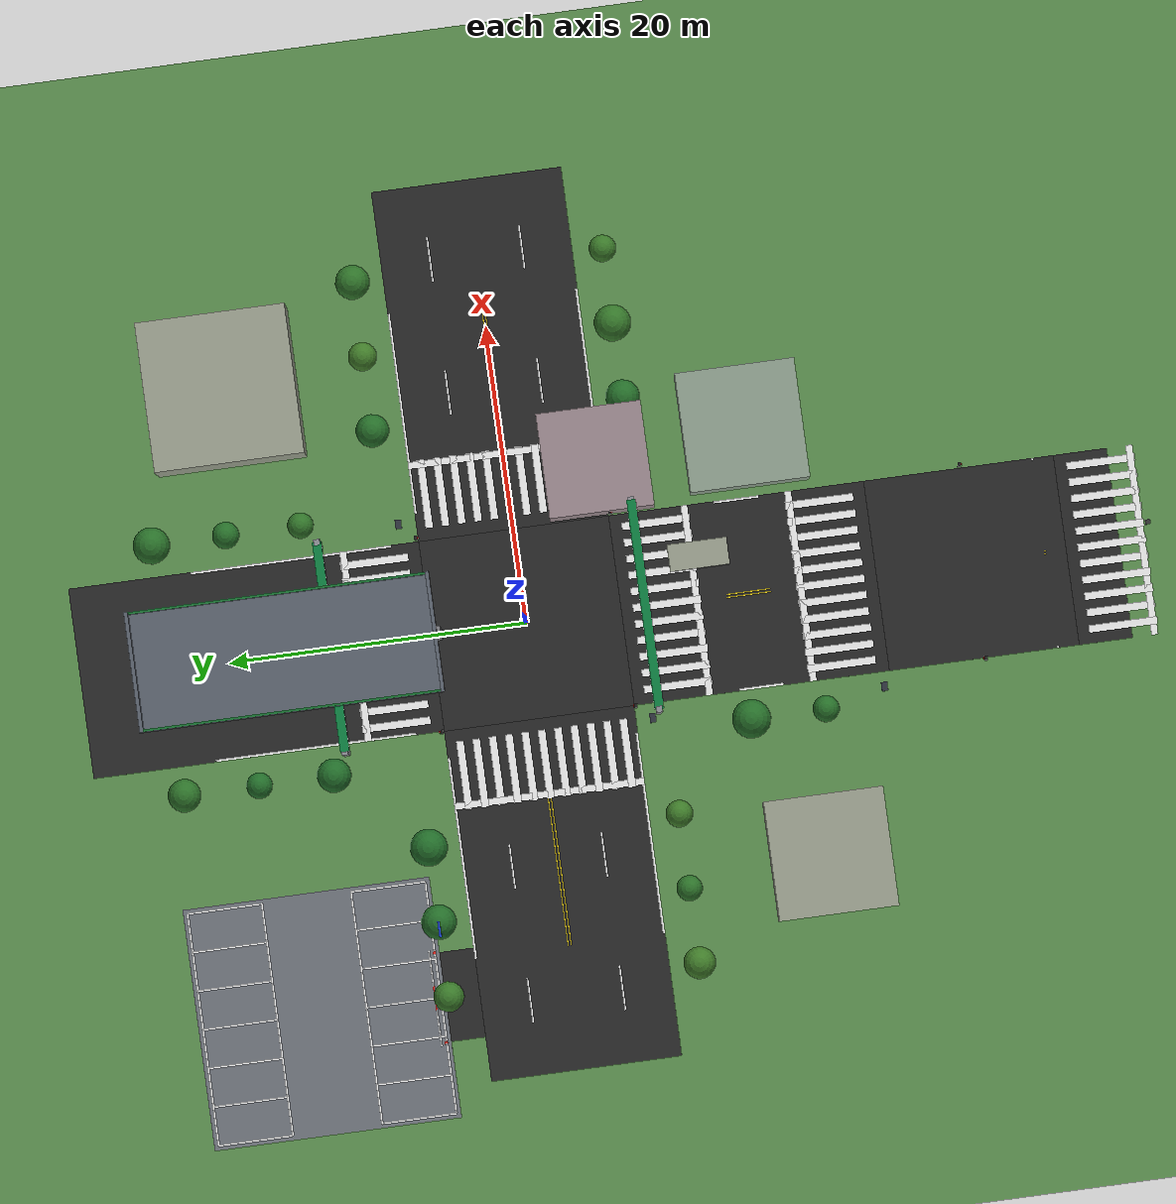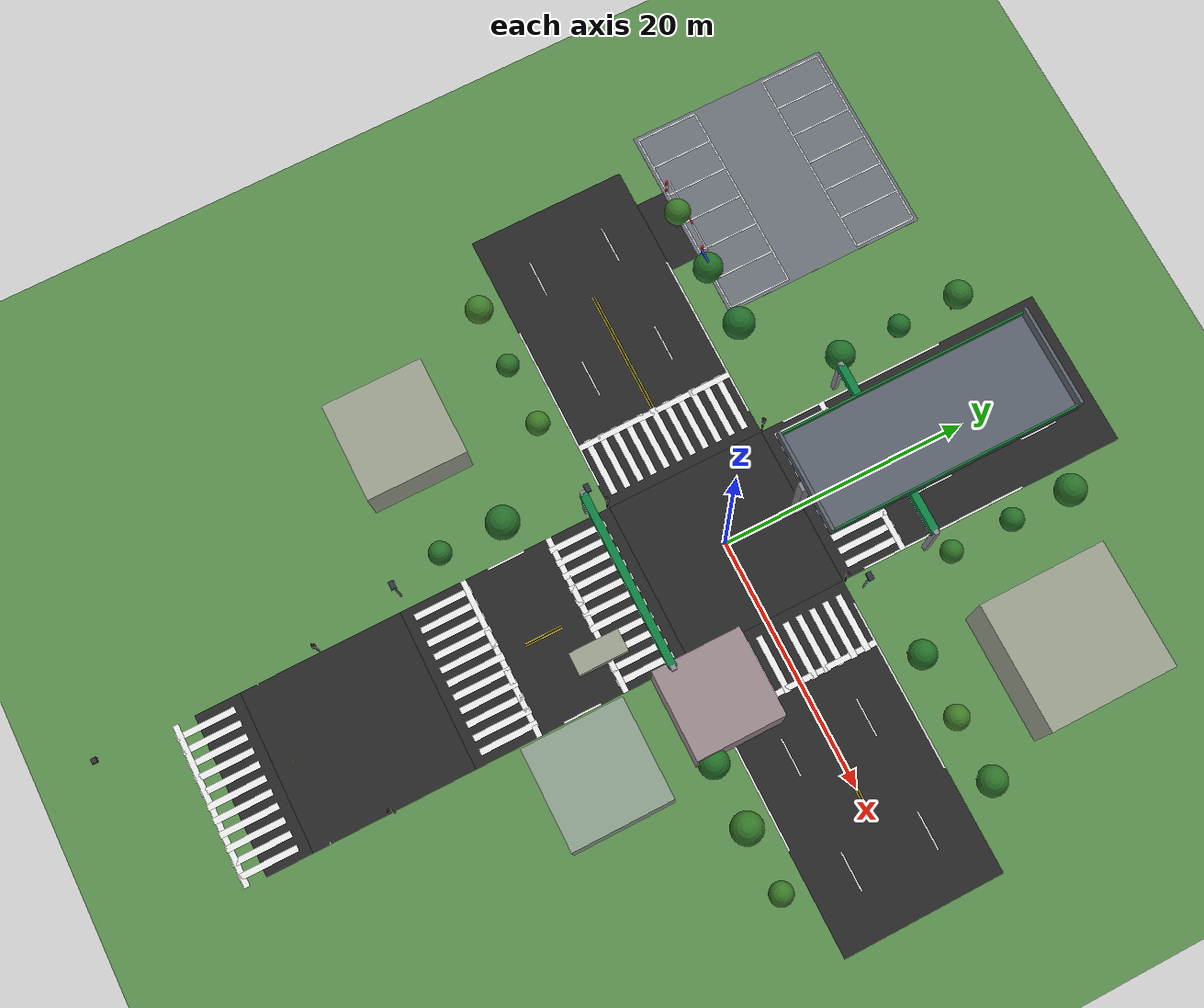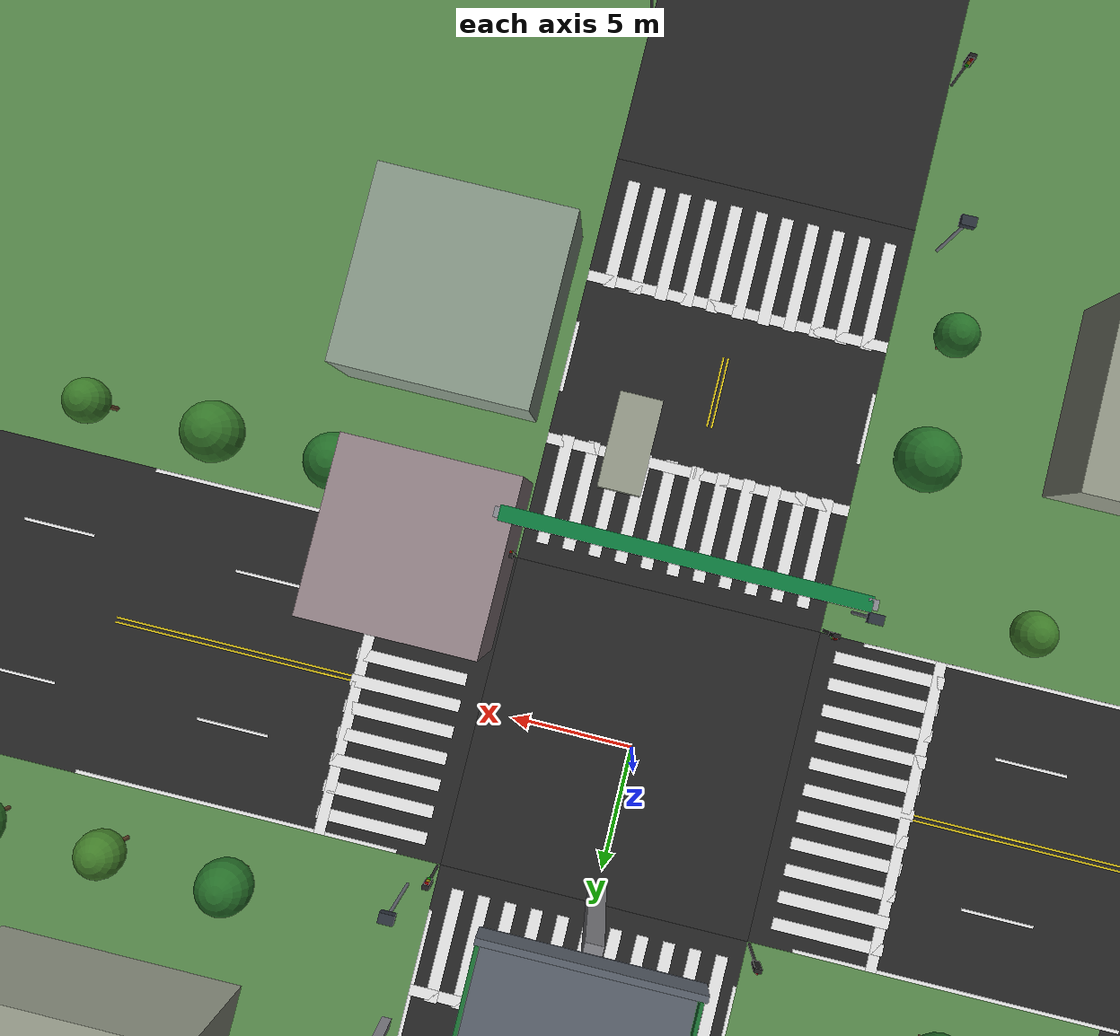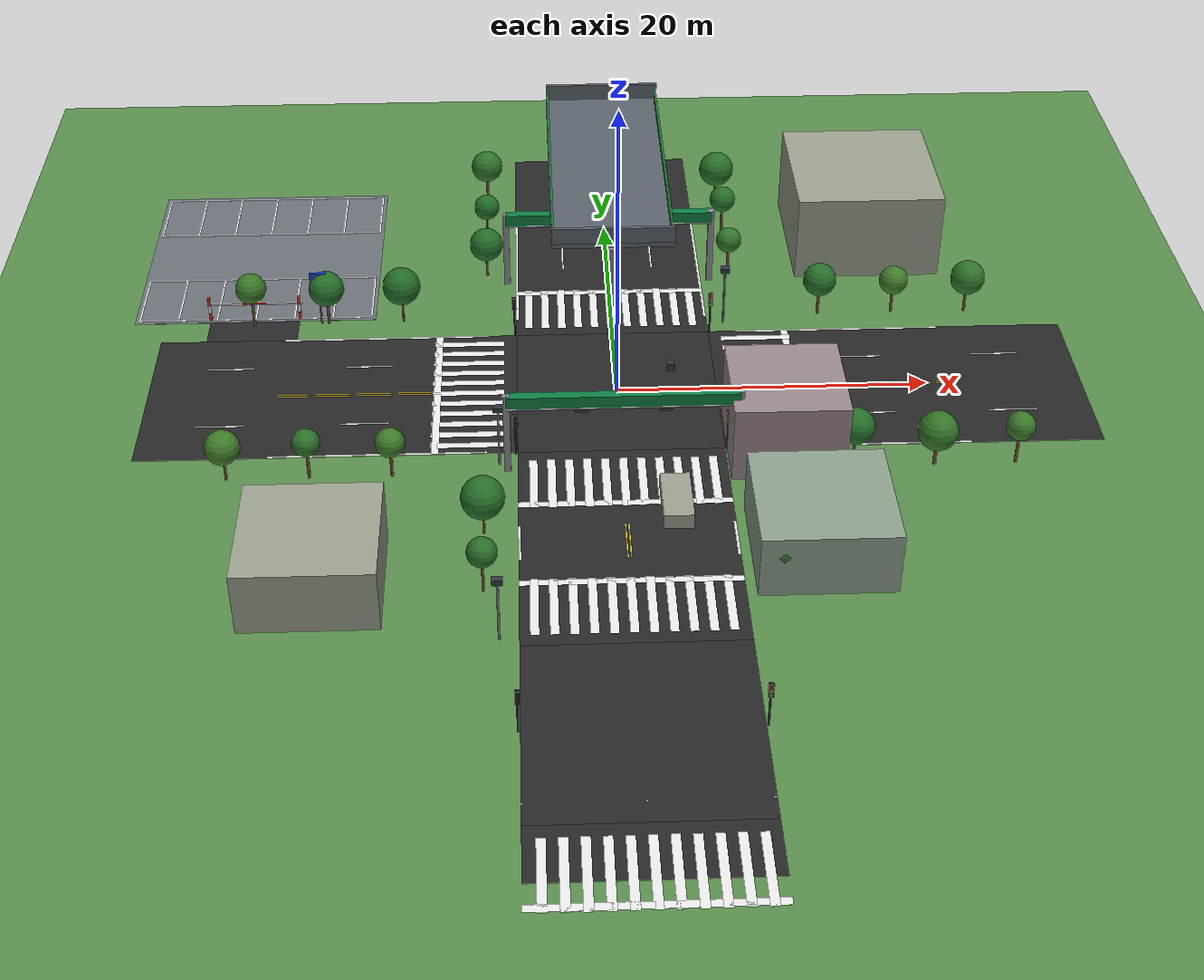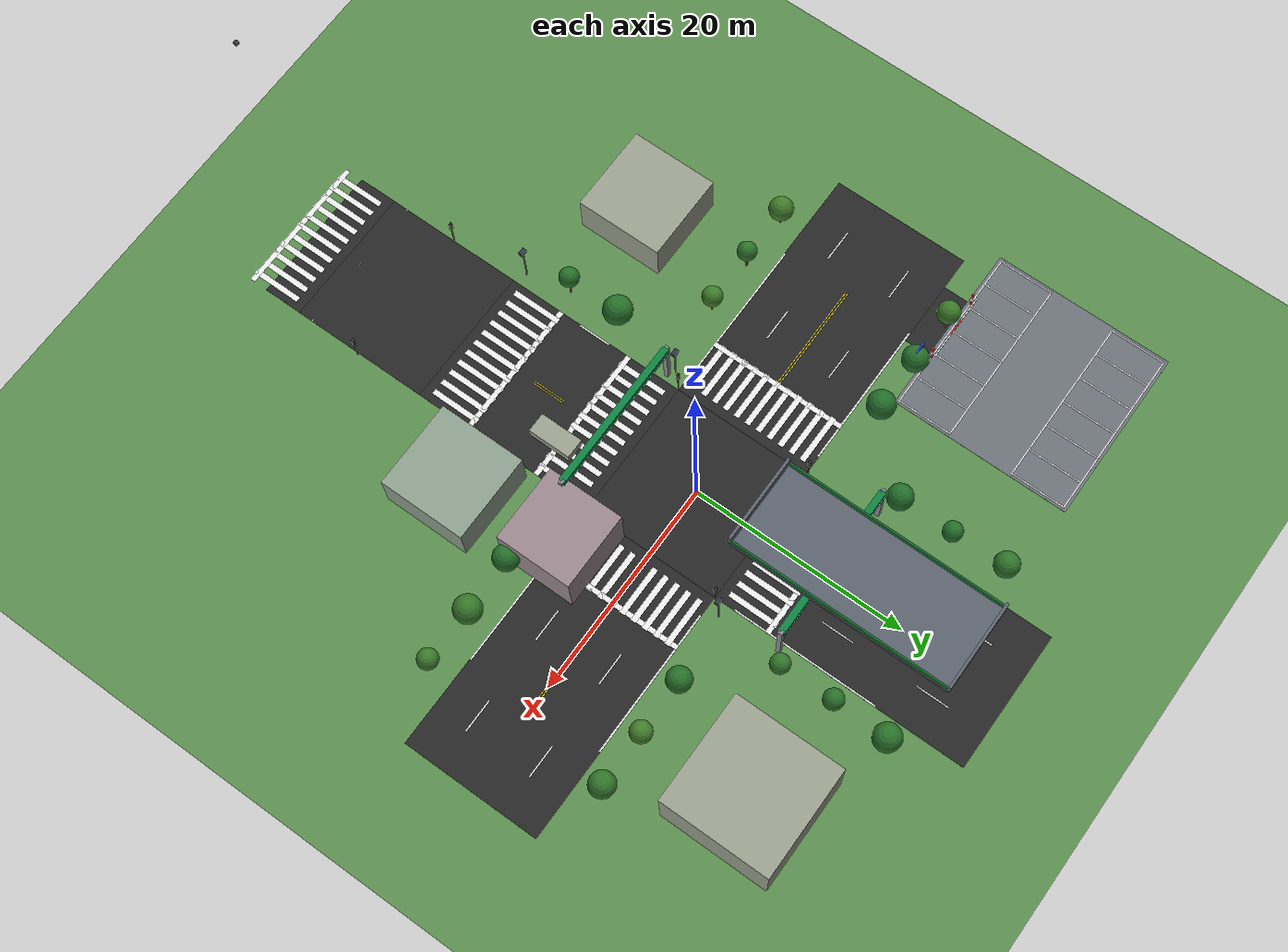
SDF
<sdf version="1.6">
 <world name="v2x_city">
  <physics type="ode">
   <real_time_update_rate>1000.0</real_time_update_rate>
   <max_step_size>0.001</max_step_size>
   <real_time_factor>1</real_time_factor>
  </physics>
  <scene><ambient>0.6 0.6 0.6 1</ambient><background>0.7 0.8 0.95 1</background><shadows>1</shadows></scene>
  <light type="directional" name="sun">
   <pose>0 0 10 0 0 0</pose>
   <diffuse>0.9 0.9 0.9 1</diffuse>
   <specular>0.2 0.2 0.2 1</specular>
   <attenuation>
    <range>1000</range>
    <constant>0.9</constant>
    <linear>0.01</linear>
    <quadratic>0.001</quadratic>
   </attenuation>
   <direction>-0.5 0.1 -0.9</direction>
  </light>
  <model name="ground_plane">
   <static>true</static>
   <link name="link">
    <collision name="collision">
     <geometry><plane><normal>0 0 1</normal><size>300 300</size></plane></geometry>
     <surface><friction><ode><mu>100</mu><mu2>50</mu2></ode></friction></surface>
    </collision>
    <visual name="visual">
     <geometry><plane><normal>0 0 1</normal><size>300 300</size></plane></geometry>
     <material><ambient>0.35 0.55 0.3 1</ambient><diffuse>0.35 0.55 0.3 1</diffuse></material>
    </visual>
   </link>
  </model>
  <plugin name="gazebo_ros_state" filename="libgazebo_ros_state.so"/>
  <model name="road_NS-north">
   <static>true</static>
   <link name="link">
    <pose>0 18.2 0.02 0 0 1.5708</pose>
    <collision name="c">
     <geometry><box><size>23.6 12.8 0.02</size></box></geometry>
     <surface><friction><ode><mu>100</mu><mu2>50</mu2></ode></friction></surface>
    </collision>
    <visual name="v">
     <geometry><box><size>23.6 12.8 0.02</size></box></geometry>
     <material><ambient>0.15 0.15 0.15 1</ambient><diffuse>0.15 0.15 0.15 1</diffuse></material>
    </visual>
   </link>
  </model>
  <model name="median_NS-north_p">
   <static>true</static>
   <link name="link">
    <pose>-0.1 15 0.032 0 0 1.5708</pose>
    <visual name="v">
     <geometry><box><size>13.5 0.08 0.004</size></box></geometry>
     <material><ambient>0.9 0.8 0.1 1</ambient><diffuse>0.9 0.8 0.1 1</diffuse></material>
    </visual>
   </link>
  </model>
  <model name="median_NS-north_m">
   <static>true</static>
   <link name="link">
    <pose>0.1 15 0.032 0 0 1.5708</pose>
    <visual name="v">
     <geometry><box><size>13.5 0.08 0.004</size></box></geometry>
     <material><ambient>0.9 0.8 0.1 1</ambient><diffuse>0.9 0.8 0.1 1</diffuse></material>
    </visual>
   </link>
  </model>
  <model name="edge_NS-north_p">
   <static>true</static>
   <link name="link">
    <pose>-6.325 15 0.032 0 0 1.5708</pose>
    <visual name="v">
     <geometry><box><size>13.5 0.15 0.004</size></box></geometry>
     <material><ambient>0.92 0.92 0.92 1</ambient><diffuse>0.92 0.92 0.92 1</diffuse></material>
    </visual>
   </link>
  </model>
  <model name="edge_NS-north_m">
   <static>true</static>
   <link name="link">
    <pose>6.325 15 0.032 0 0 1.5708</pose>
    <visual name="v">
     <geometry><box><size>13.5 0.15 0.004</size></box></geometry>
     <material><ambient>0.92 0.92 0.92 1</ambient><diffuse>0.92 0.92 0.92 1</diffuse></material>
    </visual>
   </link>
  </model>
  <model name="dash_NS-north_1_p_0">
   <static>true</static>
   <link name="link">
    <pose>-3.1 16 0.032 0 0 1.5708</pose>
    <visual name="v">
     <geometry><box><size>3 0.12 0.004</size></box></geometry>
     <material><ambient>0.92 0.92 0.92 1</ambient><diffuse>0.92 0.92 0.92 1</diffuse></material>
    </visual>
   </link>
  </model>
  <model name="dash_NS-north_1_p_1">
   <static>true</static>
   <link name="link">
    <pose>-3.1 25 0.032 0 0 1.5708</pose>
    <visual name="v">
     <geometry><box><size>3 0.12 0.004</size></box></geometry>
     <material><ambient>0.92 0.92 0.92 1</ambient><diffuse>0.92 0.92 0.92 1</diffuse></material>
    </visual>
   </link>
  </model>
  <model name="dash_NS-north_1_m_0">
   <static>true</static>
   <link name="link">
    <pose>3.1 16 0.032 0 0 1.5708</pose>
    <visual name="v">
     <geometry><box><size>3 0.12 0.004</size></box></geometry>
     <material><ambient>0.92 0.92 0.92 1</ambient><diffuse>0.92 0.92 0.92 1</diffuse></material>
    </visual>
   </link>
  </model>
  <model name="dash_NS-north_1_m_1">
   <static>true</static>
   <link name="link">
    <pose>3.1 25 0.032 0 0 1.5708</pose>
    <visual name="v">
     <geometry><box><size>3 0.12 0.004</size></box></geometry>
     <material><ambient>0.92 0.92 0.92 1</ambient><diffuse>0.92 0.92 0.92 1</diffuse></material>
    </visual>
   </link>
  </model>
  <model name="road_NS-main">
   <static>true</static>
   <link name="link">
    <pose>0 -15 0.02 0 0 -1.5708</pose>
    <collision name="c">
     <geometry><box><size>17.2 12.8 0.02</size></box></geometry>
     <surface><friction><ode><mu>100</mu><mu2>50</mu2></ode></friction></surface>
    </collision>
    <visual name="v">
     <geometry><box><size>17.2 12.8 0.02</size></box></geometry>
     <material><ambient>0.15 0.15 0.15 1</ambient><diffuse>0.15 0.15 0.15 1</diffuse></material>
    </visual>
   </link>
  </model>
  <model name="median_NS-main_p">
   <static>true</static>
   <link name="link">
    <pose>0.1 -15 0.032 0 0 -1.5708</pose>
    <visual name="v">
     <geometry><box><size>3 0.08 0.004</size></box></geometry>
     <material><ambient>0.9 0.8 0.1 1</ambient><diffuse>0.9 0.8 0.1 1</diffuse></material>
    </visual>
   </link>
  </model>
  <model name="median_NS-main_m">
   <static>true</static>
   <link name="link">
    <pose>-0.1 -15 0.032 0 0 -1.5708</pose>
    <visual name="v">
     <geometry><box><size>3 0.08 0.004</size></box></geometry>
     <material><ambient>0.9 0.8 0.1 1</ambient><diffuse>0.9 0.8 0.1 1</diffuse></material>
    </visual>
   </link>
  </model>
  <model name="edge_NS-main_p">
   <static>true</static>
   <link name="link">
    <pose>6.325 -15 0.032 0 0 -1.5708</pose>
    <visual name="v">
     <geometry><box><size>3 0.15 0.004</size></box></geometry>
     <material><ambient>0.92 0.92 0.92 1</ambient><diffuse>0.92 0.92 0.92 1</diffuse></material>
    </visual>
   </link>
  </model>
  <model name="edge_NS-main_m">
   <static>true</static>
   <link name="link">
    <pose>-6.325 -15 0.032 0 0 -1.5708</pose>
    <visual name="v">
     <geometry><box><size>3 0.15 0.004</size></box></geometry>
     <material><ambient>0.92 0.92 0.92 1</ambient><diffuse>0.92 0.92 0.92 1</diffuse></material>
    </visual>
   </link>
  </model>
  <model name="road_NS-school">
   <static>true</static>
   <link name="link">
    <pose>0 -38.2 0.02 0 0 -1.5708</pose>
    <collision name="c">
     <geometry><box><size>3.6 12.8 0.02</size></box></geometry>
     <surface><friction><ode><mu>100</mu><mu2>50</mu2></ode></friction></surface>
    </collision>
    <visual name="v">
     <geometry><box><size>3.6 12.8 0.02</size></box></geometry>
     <material><ambient>0.15 0.15 0.15 1</ambient><diffuse>0.15 0.15 0.15 1</diffuse></material>
    </visual>
   </link>
  </model>
  <model name="median_NS-school_p">
   <static>true</static>
   <link name="link">
    <pose>0.1 -35 0.032 0 0 -1.5708</pose>
    <visual name="v">
     <geometry><box><size>0.1 0.08 0.004</size></box></geometry>
     <material><ambient>0.9 0.8 0.1 1</ambient><diffuse>0.9 0.8 0.1 1</diffuse></material>
    </visual>
   </link>
  </model>
  <model name="median_NS-school_m">
   <static>true</static>
   <link name="link">
    <pose>-0.1 -35 0.032 0 0 -1.5708</pose>
    <visual name="v">
     <geometry><box><size>0.1 0.08 0.004</size></box></geometry>
     <material><ambient>0.9 0.8 0.1 1</ambient><diffuse>0.9 0.8 0.1 1</diffuse></material>
    </visual>
   </link>
  </model>
  <model name="edge_NS-school_p">
   <static>true</static>
   <link name="link">
    <pose>6.325 -35 0.032 0 0 -1.5708</pose>
    <visual name="v">
     <geometry><box><size>0.1 0.15 0.004</size></box></geometry>
     <material><ambient>0.92 0.92 0.92 1</ambient><diffuse>0.92 0.92 0.92 1</diffuse></material>
    </visual>
   </link>
  </model>
  <model name="edge_NS-school_m">
   <static>true</static>
   <link name="link">
    <pose>-6.325 -35 0.032 0 0 -1.5708</pose>
    <visual name="v">
     <geometry><box><size>0.1 0.15 0.004</size></box></geometry>
     <material><ambient>0.92 0.92 0.92 1</ambient><diffuse>0.92 0.92 0.92 1</diffuse></material>
    </visual>
   </link>
  </model>
  <model name="road_EW-east">
   <static>true</static>
   <link name="link">
    <pose>18.2 0 0.02 0 0 0</pose>
    <collision name="c">
     <geometry><box><size>23.6 12.8 0.02</size></box></geometry>
     <surface><friction><ode><mu>100</mu><mu2>50</mu2></ode></friction></surface>
    </collision>
    <visual name="v">
     <geometry><box><size>23.6 12.8 0.02</size></box></geometry>
     <material><ambient>0.15 0.15 0.15 1</ambient><diffuse>0.15 0.15 0.15 1</diffuse></material>
    </visual>
   </link>
  </model>
  <model name="median_EW-east_p">
   <static>true</static>
   <link name="link">
    <pose>15 0.1 0.032 0 0 0</pose>
    <visual name="v">
     <geometry><box><size>13.5 0.08 0.004</size></box></geometry>
     <material><ambient>0.9 0.8 0.1 1</ambient><diffuse>0.9 0.8 0.1 1</diffuse></material>
    </visual>
   </link>
  </model>
  <model name="median_EW-east_m">
   <static>true</static>
   <link name="link">
    <pose>15 -0.1 0.032 0 0 0</pose>
    <visual name="v">
     <geometry><box><size>13.5 0.08 0.004</size></box></geometry>
     <material><ambient>0.9 0.8 0.1 1</ambient><diffuse>0.9 0.8 0.1 1</diffuse></material>
    </visual>
   </link>
  </model>
  <model name="edge_EW-east_p">
   <static>true</static>
   <link name="link">
    <pose>15 6.325 0.032 0 0 0</pose>
    <visual name="v">
     <geometry><box><size>13.5 0.15 0.004</size></box></geometry>
     <material><ambient>0.92 0.92 0.92 1</ambient><diffuse>0.92 0.92 0.92 1</diffuse></material>
    </visual>
   </link>
  </model>
  <model name="edge_EW-east_m">
   <static>true</static>
   <link name="link">
    <pose>15 -6.325 0.032 0 0 0</pose>
    <visual name="v">
     <geometry><box><size>13.5 0.15 0.004</size></box></geometry>
     <material><ambient>0.92 0.92 0.92 1</ambient><diffuse>0.92 0.92 0.92 1</diffuse></material>
    </visual>
   </link>
  </model>
  <model name="dash_EW-east_1_p_0">
   <static>true</static>
   <link name="link">
    <pose>16 3.1 0.032 0 0 0</pose>
    <visual name="v">
     <geometry><box><size>3 0.12 0.004</size></box></geometry>
     <material><ambient>0.92 0.92 0.92 1</ambient><diffuse>0.92 0.92 0.92 1</diffuse></material>
    </visual>
   </link>
  </model>
  <model name="dash_EW-east_1_p_1">
   <static>true</static>
   <link name="link">
    <pose>25 3.1 0.032 0 0 0</pose>
    <visual name="v">
     <geometry><box><size>3 0.12 0.004</size></box></geometry>
     <material><ambient>0.92 0.92 0.92 1</ambient><diffuse>0.92 0.92 0.92 1</diffuse></material>
    </visual>
   </link>
  </model>
  <model name="dash_EW-east_1_m_0">
   <static>true</static>
   <link name="link">
    <pose>16 -3.1 0.032 0 0 0</pose>
    <visual name="v">
     <geometry><box><size>3 0.12 0.004</size></box></geometry>
     <material><ambient>0.92 0.92 0.92 1</ambient><diffuse>0.92 0.92 0.92 1</diffuse></material>
    </visual>
   </link>
  </model>
  <model name="dash_EW-east_1_m_1">
   <static>true</static>
   <link name="link">
    <pose>25 -3.1 0.032 0 0 0</pose>
    <visual name="v">
     <geometry><box><size>3 0.12 0.004</size></box></geometry>
     <material><ambient>0.92 0.92 0.92 1</ambient><diffuse>0.92 0.92 0.92 1</diffuse></material>
    </visual>
   </link>
  </model>
  <model name="road_EW-west">
   <static>true</static>
   <link name="link">
    <pose>-18.2 0 0.02 0 0 3.1416</pose>
    <collision name="c">
     <geometry><box><size>23.6 12.8 0.02</size></box></geometry>
     <surface><friction><ode><mu>100</mu><mu2>50</mu2></ode></friction></surface>
    </collision>
    <visual name="v">
     <geometry><box><size>23.6 12.8 0.02</size></box></geometry>
     <material><ambient>0.15 0.15 0.15 1</ambient><diffuse>0.15 0.15 0.15 1</diffuse></material>
    </visual>
   </link>
  </model>
  <model name="median_EW-west_p">
   <static>true</static>
   <link name="link">
    <pose>-15 -0.1 0.032 0 0 3.1416</pose>
    <visual name="v">
     <geometry><box><size>13.5 0.08 0.004</size></box></geometry>
     <material><ambient>0.9 0.8 0.1 1</ambient><diffuse>0.9 0.8 0.1 1</diffuse></material>
    </visual>
   </link>
  </model>
  <model name="median_EW-west_m">
   <static>true</static>
   <link name="link">
    <pose>-15 0.1 0.032 0 0 3.1416</pose>
    <visual name="v">
     <geometry><box><size>13.5 0.08 0.004</size></box></geometry>
     <material><ambient>0.9 0.8 0.1 1</ambient><diffuse>0.9 0.8 0.1 1</diffuse></material>
    </visual>
   </link>
  </model>
  <model name="edge_EW-west_p">
   <static>true</static>
   <link name="link">
    <pose>-15 -6.325 0.032 0 0 3.1416</pose>
    <visual name="v">
     <geometry><box><size>13.5 0.15 0.004</size></box></geometry>
     <material><ambient>0.92 0.92 0.92 1</ambient><diffuse>0.92 0.92 0.92 1</diffuse></material>
    </visual>
   </link>
  </model>
  <model name="edge_EW-west_m">
   <static>true</static>
   <link name="link">
    <pose>-15 6.325 0.032 0 0 3.1416</pose>
    <visual name="v">
     <geometry><box><size>13.5 0.15 0.004</size></box></geometry>
     <material><ambient>0.92 0.92 0.92 1</ambient><diffuse>0.92 0.92 0.92 1</diffuse></material>
    </visual>
   </link>
  </model>
  <model name="dash_EW-west_1_p_0">
   <static>true</static>
   <link name="link">
    <pose>-16 -3.1 0.032 0 0 3.1416</pose>
    <visual name="v">
     <geometry><box><size>3 0.12 0.004</size></box></geometry>
     <material><ambient>0.92 0.92 0.92 1</ambient><diffuse>0.92 0.92 0.92 1</diffuse></material>
    </visual>
   </link>
  </model>
  <model name="dash_EW-west_1_p_1">
   <static>true</static>
   <link name="link">
    <pose>-25 -3.1 0.032 0 0 3.1416</pose>
    <visual name="v">
     <geometry><box><size>3 0.12 0.004</size></box></geometry>
     <material><ambient>0.92 0.92 0.92 1</ambient><diffuse>0.92 0.92 0.92 1</diffuse></material>
    </visual>
   </link>
  </model>
  <model name="dash_EW-west_1_m_0">
   <static>true</static>
   <link name="link">
    <pose>-16 3.1 0.032 0 0 3.1416</pose>
    <visual name="v">
     <geometry><box><size>3 0.12 0.004</size></box></geometry>
     <material><ambient>0.92 0.92 0.92 1</ambient><diffuse>0.92 0.92 0.92 1</diffuse></material>
    </visual>
   </link>
  </model>
  <model name="dash_EW-west_1_m_1">
   <static>true</static>
   <link name="link">
    <pose>-25 3.1 0.032 0 0 3.1416</pose>
    <visual name="v">
     <geometry><box><size>3 0.12 0.004</size></box></geometry>
     <material><ambient>0.92 0.92 0.92 1</ambient><diffuse>0.92 0.92 0.92 1</diffuse></material>
    </visual>
   </link>
  </model>
  <model name="junction_J1">
   <static>true</static>
   <link name="link">
    <pose>0 0 0.02 0 0 0</pose>
    <collision name="c">
     <geometry><box><size>12.8 12.8 0.02</size></box></geometry>
     <surface><friction><ode><mu>100</mu><mu2>50</mu2></ode></friction></surface>
    </collision>
    <visual name="v">
     <geometry><box><size>12.8 12.8 0.02</size></box></geometry>
     <material><ambient>0.15 0.15 0.15 1</ambient><diffuse>0.15 0.15 0.15 1</diffuse></material>
    </visual>
   </link>
  </model>
  <model name="junction_J2">
   <static>true</static>
   <link name="link">
    <pose>0 -30 0.02 0 0 0</pose>
    <collision name="c">
     <geometry><box><size>12.8 12.8 0.02</size></box></geometry>
     <surface><friction><ode><mu>100</mu><mu2>50</mu2></ode></friction></surface>
    </collision>
    <visual name="v">
     <geometry><box><size>12.8 12.8 0.02</size></box></geometry>
     <material><ambient>0.15 0.15 0.15 1</ambient><diffuse>0.15 0.15 0.15 1</diffuse></material>
    </visual>
   </link>
  </model>
  <model name="zebra_J1_NS-north_0">
   <static>true</static>
   <link name="link">
    <pose>5.45 9.5 0.034 0 0 1.5708</pose>
    <visual name="v">
     <geometry><box><size>4.6 0.5 0.004</size></box></geometry>
     <material><ambient>0.92 0.92 0.92 1</ambient><diffuse>0.92 0.92 0.92 1</diffuse></material>
    </visual>
   </link>
  </model>
  <model name="zebra_J1_NS-north_1">
   <static>true</static>
   <link name="link">
    <pose>4.35 9.5 0.034 0 0 1.5708</pose>
    <visual name="v">
     <geometry><box><size>4.6 0.5 0.004</size></box></geometry>
     <material><ambient>0.92 0.92 0.92 1</ambient><diffuse>0.92 0.92 0.92 1</diffuse></material>
    </visual>
   </link>
  </model>
  <model name="zebra_J1_NS-north_2">
   <static>true</static>
   <link name="link">
    <pose>3.25 9.5 0.034 0 0 1.5708</pose>
    <visual name="v">
     <geometry><box><size>4.6 0.5 0.004</size></box></geometry>
     <material><ambient>0.92 0.92 0.92 1</ambient><diffuse>0.92 0.92 0.92 1</diffuse></material>
    </visual>
   </link>
  </model>
  <model name="zebra_J1_NS-north_3">
   <static>true</static>
   <link name="link">
    <pose>2.15 9.5 0.034 0 0 1.5708</pose>
    <visual name="v">
     <geometry><box><size>4.6 0.5 0.004</size></box></geometry>
     <material><ambient>0.92 0.92 0.92 1</ambient><diffuse>0.92 0.92 0.92 1</diffuse></material>
    </visual>
   </link>
  </model>
  <model name="zebra_J1_NS-north_4">
   <static>true</static>
   <link name="link">
    <pose>1.05 9.5 0.034 0 0 1.5708</pose>
    <visual name="v">
     <geometry><box><size>4.6 0.5 0.004</size></box></geometry>
     <material><ambient>0.92 0.92 0.92 1</ambient><diffuse>0.92 0.92 0.92 1</diffuse></material>
    </visual>
   </link>
  </model>
  <model name="zebra_J1_NS-north_5">
   <static>true</static>
   <link name="link">
    <pose>-0.05 9.5 0.034 0 0 1.5708</pose>
    <visual name="v">
     <geometry><box><size>4.6 0.5 0.004</size></box></geometry>
     <material><ambient>0.92 0.92 0.92 1</ambient><diffuse>0.92 0.92 0.92 1</diffuse></material>
    </visual>
   </link>
  </model>
  <model name="zebra_J1_NS-north_6">
   <static>true</static>
   <link name="link">
    <pose>-1.15 9.5 0.034 0 0 1.5708</pose>
    <visual name="v">
     <geometry><box><size>4.6 0.5 0.004</size></box></geometry>
     <material><ambient>0.92 0.92 0.92 1</ambient><diffuse>0.92 0.92 0.92 1</diffuse></material>
    </visual>
   </link>
  </model>
  <model name="zebra_J1_NS-north_7">
   <static>true</static>
   <link name="link">
    <pose>-2.25 9.5 0.034 0 0 1.5708</pose>
    <visual name="v">
     <geometry><box><size>4.6 0.5 0.004</size></box></geometry>
     <material><ambient>0.92 0.92 0.92 1</ambient><diffuse>0.92 0.92 0.92 1</diffuse></material>
    </visual>
   </link>
  </model>
  <model name="zebra_J1_NS-north_8">
   <static>true</static>
   <link name="link">
    <pose>-3.35 9.5 0.034 0 0 1.5708</pose>
    <visual name="v">
     <geometry><box><size>4.6 0.5 0.004</size></box></geometry>
     <material><ambient>0.92 0.92 0.92 1</ambient><diffuse>0.92 0.92 0.92 1</diffuse></material>
    </visual>
   </link>
  </model>
  <model name="zebra_J1_NS-north_9">
   <static>true</static>
   <link name="link">
    <pose>-4.45 9.5 0.034 0 0 1.5708</pose>
    <visual name="v">
     <geometry><box><size>4.6 0.5 0.004</size></box></geometry>
     <material><ambient>0.92 0.92 0.92 1</ambient><diffuse>0.92 0.92 0.92 1</diffuse></material>
    </visual>
   </link>
  </model>
  <model name="zebra_J1_NS-north_10">
   <static>true</static>
   <link name="link">
    <pose>-5.55 9.5 0.034 0 0 1.5708</pose>
    <visual name="v">
     <geometry><box><size>4.6 0.5 0.004</size></box></geometry>
     <material><ambient>0.92 0.92 0.92 1</ambient><diffuse>0.92 0.92 0.92 1</diffuse></material>
    </visual>
   </link>
  </model>
  <model name="stopline_J1_NS-north_p">
   <static>true</static>
   <link name="link">
    <pose>-3.25 11.5 0.034 0 0 1.5708</pose>
    <visual name="v">
     <geometry><box><size>0.45 6.3 0.004</size></box></geometry>
     <material><ambient>0.92 0.92 0.92 1</ambient><diffuse>0.92 0.92 0.92 1</diffuse></material>
    </visual>
   </link>
  </model>
  <model name="stopline_J1_NS-north_m">
   <static>true</static>
   <link name="link">
    <pose>3.25 11.5 0.034 0 0 1.5708</pose>
    <visual name="v">
     <geometry><box><size>0.45 6.3 0.004</size></box></geometry>
     <material><ambient>0.92 0.92 0.92 1</ambient><diffuse>0.92 0.92 0.92 1</diffuse></material>
    </visual>
   </link>
  </model>
  <model name="zebra_J1_NS-main_0">
   <static>true</static>
   <link name="link">
    <pose>-5.45 -9.5 0.034 0 0 -1.5708</pose>
    <visual name="v">
     <geometry><box><size>4.6 0.5 0.004</size></box></geometry>
     <material><ambient>0.92 0.92 0.92 1</ambient><diffuse>0.92 0.92 0.92 1</diffuse></material>
    </visual>
   </link>
  </model>
  <model name="zebra_J1_NS-main_1">
   <static>true</static>
   <link name="link">
    <pose>-4.35 -9.5 0.034 0 0 -1.5708</pose>
    <visual name="v">
     <geometry><box><size>4.6 0.5 0.004</size></box></geometry>
     <material><ambient>0.92 0.92 0.92 1</ambient><diffuse>0.92 0.92 0.92 1</diffuse></material>
    </visual>
   </link>
  </model>
  <model name="zebra_J1_NS-main_2">
   <static>true</static>
   <link name="link">
    <pose>-3.25 -9.5 0.034 0 0 -1.5708</pose>
    <visual name="v">
     <geometry><box><size>4.6 0.5 0.004</size></box></geometry>
     <material><ambient>0.92 0.92 0.92 1</ambient><diffuse>0.92 0.92 0.92 1</diffuse></material>
    </visual>
   </link>
  </model>
  <model name="zebra_J1_NS-main_3">
   <static>true</static>
   <link name="link">
    <pose>-2.15 -9.5 0.034 0 0 -1.5708</pose>
    <visual name="v">
     <geometry><box><size>4.6 0.5 0.004</size></box></geometry>
     <material><ambient>0.92 0.92 0.92 1</ambient><diffuse>0.92 0.92 0.92 1</diffuse></material>
    </visual>
   </link>
  </model>
  <model name="zebra_J1_NS-main_4">
   <static>true</static>
   <link name="link">
    <pose>-1.05 -9.5 0.034 0 0 -1.5708</pose>
    <visual name="v">
     <geometry><box><size>4.6 0.5 0.004</size></box></geometry>
     <material><ambient>0.92 0.92 0.92 1</ambient><diffuse>0.92 0.92 0.92 1</diffuse></material>
    </visual>
   </link>
  </model>
  <model name="zebra_J1_NS-main_5">
   <static>true</static>
   <link name="link">
    <pose>0.05 -9.5 0.034 0 0 -1.5708</pose>
    <visual name="v">
     <geometry><box><size>4.6 0.5 0.004</size></box></geometry>
     <material><ambient>0.92 0.92 0.92 1</ambient><diffuse>0.92 0.92 0.92 1</diffuse></material>
    </visual>
   </link>
  </model>
  <model name="zebra_J1_NS-main_6">
   <static>true</static>
   <link name="link">
    <pose>1.15 -9.5 0.034 0 0 -1.5708</pose>
    <visual name="v">
     <geometry><box><size>4.6 0.5 0.004</size></box></geometry>
     <material><ambient>0.92 0.92 0.92 1</ambient><diffuse>0.92 0.92 0.92 1</diffuse></material>
    </visual>
   </link>
  </model>
  <model name="zebra_J1_NS-main_7">
   <static>true</static>
   <link name="link">
    <pose>2.25 -9.5 0.034 0 0 -1.5708</pose>
    <visual name="v">
     <geometry><box><size>4.6 0.5 0.004</size></box></geometry>
     <material><ambient>0.92 0.92 0.92 1</ambient><diffuse>0.92 0.92 0.92 1</diffuse></material>
    </visual>
   </link>
  </model>
  <model name="zebra_J1_NS-main_8">
   <static>true</static>
   <link name="link">
    <pose>3.35 -9.5 0.034 0 0 -1.5708</pose>
    <visual name="v">
     <geometry><box><size>4.6 0.5 0.004</size></box></geometry>
     <material><ambient>0.92 0.92 0.92 1</ambient><diffuse>0.92 0.92 0.92 1</diffuse></material>
    </visual>
   </link>
  </model>
  <model name="zebra_J1_NS-main_9">
   <static>true</static>
   <link name="link">
    <pose>4.45 -9.5 0.034 0 0 -1.5708</pose>
    <visual name="v">
     <geometry><box><size>4.6 0.5 0.004</size></box></geometry>
     <material><ambient>0.92 0.92 0.92 1</ambient><diffuse>0.92 0.92 0.92 1</diffuse></material>
    </visual>
   </link>
  </model>
  <model name="zebra_J1_NS-main_10">
   <static>true</static>
   <link name="link">
    <pose>5.55 -9.5 0.034 0 0 -1.5708</pose>
    <visual name="v">
     <geometry><box><size>4.6 0.5 0.004</size></box></geometry>
     <material><ambient>0.92 0.92 0.92 1</ambient><diffuse>0.92 0.92 0.92 1</diffuse></material>
    </visual>
   </link>
  </model>
  <model name="stopline_J1_NS-main_p">
   <static>true</static>
   <link name="link">
    <pose>3.25 -11.5 0.034 0 0 -1.5708</pose>
    <visual name="v">
     <geometry><box><size>0.45 6.3 0.004</size></box></geometry>
     <material><ambient>0.92 0.92 0.92 1</ambient><diffuse>0.92 0.92 0.92 1</diffuse></material>
    </visual>
   </link>
  </model>
  <model name="stopline_J1_NS-main_m">
   <static>true</static>
   <link name="link">
    <pose>-3.25 -11.5 0.034 0 0 -1.5708</pose>
    <visual name="v">
     <geometry><box><size>0.45 6.3 0.004</size></box></geometry>
     <material><ambient>0.92 0.92 0.92 1</ambient><diffuse>0.92 0.92 0.92 1</diffuse></material>
    </visual>
   </link>
  </model>
  <model name="zebra_J1_EW-east_0">
   <static>true</static>
   <link name="link">
    <pose>9.5 -5.45 0.034 0 0 0</pose>
    <visual name="v">
     <geometry><box><size>4.6 0.5 0.004</size></box></geometry>
     <material><ambient>0.92 0.92 0.92 1</ambient><diffuse>0.92 0.92 0.92 1</diffuse></material>
    </visual>
   </link>
  </model>
  <model name="zebra_J1_EW-east_1">
   <static>true</static>
   <link name="link">
    <pose>9.5 -4.35 0.034 0 0 0</pose>
    <visual name="v">
     <geometry><box><size>4.6 0.5 0.004</size></box></geometry>
     <material><ambient>0.92 0.92 0.92 1</ambient><diffuse>0.92 0.92 0.92 1</diffuse></material>
    </visual>
   </link>
  </model>
  <model name="zebra_J1_EW-east_2">
   <static>true</static>
   <link name="link">
    <pose>9.5 -3.25 0.034 0 0 0</pose>
    <visual name="v">
     <geometry><box><size>4.6 0.5 0.004</size></box></geometry>
     <material><ambient>0.92 0.92 0.92 1</ambient><diffuse>0.92 0.92 0.92 1</diffuse></material>
    </visual>
   </link>
  </model>
  <model name="zebra_J1_EW-east_3">
   <static>true</static>
   <link name="link">
    <pose>9.5 -2.15 0.034 0 0 0</pose>
    <visual name="v">
     <geometry><box><size>4.6 0.5 0.004</size></box></geometry>
     <material><ambient>0.92 0.92 0.92 1</ambient><diffuse>0.92 0.92 0.92 1</diffuse></material>
    </visual>
   </link>
  </model>
  <model name="zebra_J1_EW-east_4">
   <static>true</static>
   <link name="link">
    <pose>9.5 -1.05 0.034 0 0 0</pose>
    <visual name="v">
     <geometry><box><size>4.6 0.5 0.004</size></box></geometry>
     <material><ambient>0.92 0.92 0.92 1</ambient><diffuse>0.92 0.92 0.92 1</diffuse></material>
    </visual>
   </link>
  </model>
  <model name="zebra_J1_EW-east_5">
   <static>true</static>
   <link name="link">
    <pose>9.5 0.05 0.034 0 0 0</pose>
    <visual name="v">
     <geometry><box><size>4.6 0.5 0.004</size></box></geometry>
     <material><ambient>0.92 0.92 0.92 1</ambient><diffuse>0.92 0.92 0.92 1</diffuse></material>
    </visual>
   </link>
  </model>
  <model name="zebra_J1_EW-east_6">
   <static>true</static>
   <link name="link">
    <pose>9.5 1.15 0.034 0 0 0</pose>
    <visual name="v">
     <geometry><box><size>4.6 0.5 0.004</size></box></geometry>
     <material><ambient>0.92 0.92 0.92 1</ambient><diffuse>0.92 0.92 0.92 1</diffuse></material>
    </visual>
   </link>
  </model>
  <model name="zebra_J1_EW-east_7">
   <static>true</static>
   <link name="link">
    <pose>9.5 2.25 0.034 0 0 0</pose>
    <visual name="v">
     <geometry><box><size>4.6 0.5 0.004</size></box></geometry>
     <material><ambient>0.92 0.92 0.92 1</ambient><diffuse>0.92 0.92 0.92 1</diffuse></material>
    </visual>
   </link>
  </model>
  <model name="zebra_J1_EW-east_8">
   <static>true</static>
   <link name="link">
    <pose>9.5 3.35 0.034 0 0 0</pose>
    <visual name="v">
     <geometry><box><size>4.6 0.5 0.004</size></box></geometry>
     <material><ambient>0.92 0.92 0.92 1</ambient><diffuse>0.92 0.92 0.92 1</diffuse></material>
    </visual>
   </link>
  </model>
  <model name="zebra_J1_EW-east_9">
   <static>true</static>
   <link name="link">
    <pose>9.5 4.45 0.034 0 0 0</pose>
    <visual name="v">
     <geometry><box><size>4.6 0.5 0.004</size></box></geometry>
     <material><ambient>0.92 0.92 0.92 1</ambient><diffuse>0.92 0.92 0.92 1</diffuse></material>
    </visual>
   </link>
  </model>
  <model name="zebra_J1_EW-east_10">
   <static>true</static>
   <link name="link">
    <pose>9.5 5.55 0.034 0 0 0</pose>
    <visual name="v">
     <geometry><box><size>4.6 0.5 0.004</size></box></geometry>
     <material><ambient>0.92 0.92 0.92 1</ambient><diffuse>0.92 0.92 0.92 1</diffuse></material>
    </visual>
   </link>
  </model>
  <model name="stopline_J1_EW-east_p">
   <static>true</static>
   <link name="link">
    <pose>11.5 3.25 0.034 0 0 0</pose>
    <visual name="v">
     <geometry><box><size>0.45 6.3 0.004</size></box></geometry>
     <material><ambient>0.92 0.92 0.92 1</ambient><diffuse>0.92 0.92 0.92 1</diffuse></material>
    </visual>
   </link>
  </model>
  <model name="stopline_J1_EW-east_m">
   <static>true</static>
   <link name="link">
    <pose>11.5 -3.25 0.034 0 0 0</pose>
    <visual name="v">
     <geometry><box><size>0.45 6.3 0.004</size></box></geometry>
     <material><ambient>0.92 0.92 0.92 1</ambient><diffuse>0.92 0.92 0.92 1</diffuse></material>
    </visual>
   </link>
  </model>
  <model name="zebra_J1_EW-west_0">
   <static>true</static>
   <link name="link">
    <pose>-9.5 5.45 0.034 0 0 3.1416</pose>
    <visual name="v">
     <geometry><box><size>4.6 0.5 0.004</size></box></geometry>
     <material><ambient>0.92 0.92 0.92 1</ambient><diffuse>0.92 0.92 0.92 1</diffuse></material>
    </visual>
   </link>
  </model>
  <model name="zebra_J1_EW-west_1">
   <static>true</static>
   <link name="link">
    <pose>-9.5 4.35 0.034 0 0 3.1416</pose>
    <visual name="v">
     <geometry><box><size>4.6 0.5 0.004</size></box></geometry>
     <material><ambient>0.92 0.92 0.92 1</ambient><diffuse>0.92 0.92 0.92 1</diffuse></material>
    </visual>
   </link>
  </model>
  <model name="zebra_J1_EW-west_2">
   <static>true</static>
   <link name="link">
    <pose>-9.5 3.25 0.034 0 0 3.1416</pose>
    <visual name="v">
     <geometry><box><size>4.6 0.5 0.004</size></box></geometry>
     <material><ambient>0.92 0.92 0.92 1</ambient><diffuse>0.92 0.92 0.92 1</diffuse></material>
    </visual>
   </link>
  </model>
  <model name="zebra_J1_EW-west_3">
   <static>true</static>
   <link name="link">
    <pose>-9.5 2.15 0.034 0 0 3.1416</pose>
    <visual name="v">
     <geometry><box><size>4.6 0.5 0.004</size></box></geometry>
     <material><ambient>0.92 0.92 0.92 1</ambient><diffuse>0.92 0.92 0.92 1</diffuse></material>
    </visual>
   </link>
  </model>
  <model name="zebra_J1_EW-west_4">
   <static>true</static>
   <link name="link">
    <pose>-9.5 1.05 0.034 0 0 3.1416</pose>
    <visual name="v">
     <geometry><box><size>4.6 0.5 0.004</size></box></geometry>
     <material><ambient>0.92 0.92 0.92 1</ambient><diffuse>0.92 0.92 0.92 1</diffuse></material>
    </visual>
   </link>
  </model>
  <model name="zebra_J1_EW-west_5">
   <static>true</static>
   <link name="link">
    <pose>-9.5 -0.05 0.034 0 0 3.1416</pose>
    <visual name="v">
     <geometry><box><size>4.6 0.5 0.004</size></box></geometry>
     <material><ambient>0.92 0.92 0.92 1</ambient><diffuse>0.92 0.92 0.92 1</diffuse></material>
    </visual>
   </link>
  </model>
  <model name="zebra_J1_EW-west_6">
   <static>true</static>
   <link name="link">
    <pose>-9.5 -1.15 0.034 0 0 3.1416</pose>
    <visual name="v">
     <geometry><box><size>4.6 0.5 0.004</size></box></geometry>
     <material><ambient>0.92 0.92 0.92 1</ambient><diffuse>0.92 0.92 0.92 1</diffuse></material>
    </visual>
   </link>
  </model>
  <model name="zebra_J1_EW-west_7">
   <static>true</static>
   <link name="link">
    <pose>-9.5 -2.25 0.034 0 0 3.1416</pose>
    <visual name="v">
     <geometry><box><size>4.6 0.5 0.004</size></box></geometry>
     <material><ambient>0.92 0.92 0.92 1</ambient><diffuse>0.92 0.92 0.92 1</diffuse></material>
    </visual>
   </link>
  </model>
  <model name="zebra_J1_EW-west_8">
   <static>true</static>
   <link name="link">
    <pose>-9.5 -3.35 0.034 0 0 3.1416</pose>
    <visual name="v">
     <geometry><box><size>4.6 0.5 0.004</size></box></geometry>
     <material><ambient>0.92 0.92 0.92 1</ambient><diffuse>0.92 0.92 0.92 1</diffuse></material>
    </visual>
   </link>
  </model>
  <model name="zebra_J1_EW-west_9">
   <static>true</static>
   <link name="link">
    <pose>-9.5 -4.45 0.034 0 0 3.1416</pose>
    <visual name="v">
     <geometry><box><size>4.6 0.5 0.004</size></box></geometry>
     <material><ambient>0.92 0.92 0.92 1</ambient><diffuse>0.92 0.92 0.92 1</diffuse></material>
    </visual>
   </link>
  </model>
  <model name="zebra_J1_EW-west_10">
   <static>true</static>
   <link name="link">
    <pose>-9.5 -5.55 0.034 0 0 3.1416</pose>
    <visual name="v">
     <geometry><box><size>4.6 0.5 0.004</size></box></geometry>
     <material><ambient>0.92 0.92 0.92 1</ambient><diffuse>0.92 0.92 0.92 1</diffuse></material>
    </visual>
   </link>
  </model>
  <model name="stopline_J1_EW-west_p">
   <static>true</static>
   <link name="link">
    <pose>-11.5 -3.25 0.034 0 0 3.1416</pose>
    <visual name="v">
     <geometry><box><size>0.45 6.3 0.004</size></box></geometry>
     <material><ambient>0.92 0.92 0.92 1</ambient><diffuse>0.92 0.92 0.92 1</diffuse></material>
    </visual>
   </link>
  </model>
  <model name="stopline_J1_EW-west_m">
   <static>true</static>
   <link name="link">
    <pose>-11.5 3.25 0.034 0 0 3.1416</pose>
    <visual name="v">
     <geometry><box><size>0.45 6.3 0.004</size></box></geometry>
     <material><ambient>0.92 0.92 0.92 1</ambient><diffuse>0.92 0.92 0.92 1</diffuse></material>
    </visual>
   </link>
  </model>
  <model name="zebra_J2_NS-main_0">
   <static>true</static>
   <link name="link">
    <pose>5.45 -20.5 0.034 0 0 1.5708</pose>
    <visual name="v">
     <geometry><box><size>4.6 0.5 0.004</size></box></geometry>
     <material><ambient>0.92 0.92 0.92 1</ambient><diffuse>0.92 0.92 0.92 1</diffuse></material>
    </visual>
   </link>
  </model>
  <model name="zebra_J2_NS-main_1">
   <static>true</static>
   <link name="link">
    <pose>4.35 -20.5 0.034 0 0 1.5708</pose>
    <visual name="v">
     <geometry><box><size>4.6 0.5 0.004</size></box></geometry>
     <material><ambient>0.92 0.92 0.92 1</ambient><diffuse>0.92 0.92 0.92 1</diffuse></material>
    </visual>
   </link>
  </model>
  <model name="zebra_J2_NS-main_2">
   <static>true</static>
   <link name="link">
    <pose>3.25 -20.5 0.034 0 0 1.5708</pose>
    <visual name="v">
     <geometry><box><size>4.6 0.5 0.004</size></box></geometry>
     <material><ambient>0.92 0.92 0.92 1</ambient><diffuse>0.92 0.92 0.92 1</diffuse></material>
    </visual>
   </link>
  </model>
  <model name="zebra_J2_NS-main_3">
   <static>true</static>
   <link name="link">
    <pose>2.15 -20.5 0.034 0 0 1.5708</pose>
    <visual name="v">
     <geometry><box><size>4.6 0.5 0.004</size></box></geometry>
     <material><ambient>0.92 0.92 0.92 1</ambient><diffuse>0.92 0.92 0.92 1</diffuse></material>
    </visual>
   </link>
  </model>
  <model name="zebra_J2_NS-main_4">
   <static>true</static>
   <link name="link">
    <pose>1.05 -20.5 0.034 0 0 1.5708</pose>
    <visual name="v">
     <geometry><box><size>4.6 0.5 0.004</size></box></geometry>
     <material><ambient>0.92 0.92 0.92 1</ambient><diffuse>0.92 0.92 0.92 1</diffuse></material>
    </visual>
   </link>
  </model>
  <model name="zebra_J2_NS-main_5">
   <static>true</static>
   <link name="link">
    <pose>-0.05 -20.5 0.034 0 0 1.5708</pose>
    <visual name="v">
     <geometry><box><size>4.6 0.5 0.004</size></box></geometry>
     <material><ambient>0.92 0.92 0.92 1</ambient><diffuse>0.92 0.92 0.92 1</diffuse></material>
    </visual>
   </link>
  </model>
  <model name="zebra_J2_NS-main_6">
   <static>true</static>
   <link name="link">
    <pose>-1.15 -20.5 0.034 0 0 1.5708</pose>
    <visual name="v">
     <geometry><box><size>4.6 0.5 0.004</size></box></geometry>
     <material><ambient>0.92 0.92 0.92 1</ambient><diffuse>0.92 0.92 0.92 1</diffuse></material>
    </visual>
   </link>
  </model>
  <model name="zebra_J2_NS-main_7">
   <static>true</static>
   <link name="link">
    <pose>-2.25 -20.5 0.034 0 0 1.5708</pose>
    <visual name="v">
     <geometry><box><size>4.6 0.5 0.004</size></box></geometry>
     <material><ambient>0.92 0.92 0.92 1</ambient><diffuse>0.92 0.92 0.92 1</diffuse></material>
    </visual>
   </link>
  </model>
  <model name="zebra_J2_NS-main_8">
   <static>true</static>
   <link name="link">
    <pose>-3.35 -20.5 0.034 0 0 1.5708</pose>
    <visual name="v">
     <geometry><box><size>4.6 0.5 0.004</size></box></geometry>
     <material><ambient>0.92 0.92 0.92 1</ambient><diffuse>0.92 0.92 0.92 1</diffuse></material>
    </visual>
   </link>
  </model>
  <model name="zebra_J2_NS-main_9">
   <static>true</static>
   <link name="link">
    <pose>-4.45 -20.5 0.034 0 0 1.5708</pose>
    <visual name="v">
     <geometry><box><size>4.6 0.5 0.004</size></box></geometry>
     <material><ambient>0.92 0.92 0.92 1</ambient><diffuse>0.92 0.92 0.92 1</diffuse></material>
    </visual>
   </link>
  </model>
  <model name="zebra_J2_NS-main_10">
   <static>true</static>
   <link name="link">
    <pose>-5.55 -20.5 0.034 0 0 1.5708</pose>
    <visual name="v">
     <geometry><box><size>4.6 0.5 0.004</size></box></geometry>
     <material><ambient>0.92 0.92 0.92 1</ambient><diffuse>0.92 0.92 0.92 1</diffuse></material>
    </visual>
   </link>
  </model>
  <model name="stopline_J2_NS-main_p">
   <static>true</static>
   <link name="link">
    <pose>-3.25 -18.5 0.034 0 0 1.5708</pose>
    <visual name="v">
     <geometry><box><size>0.45 6.3 0.004</size></box></geometry>
     <material><ambient>0.92 0.92 0.92 1</ambient><diffuse>0.92 0.92 0.92 1</diffuse></material>
    </visual>
   </link>
  </model>
  <model name="stopline_J2_NS-main_m">
   <static>true</static>
   <link name="link">
    <pose>3.25 -18.5 0.034 0 0 1.5708</pose>
    <visual name="v">
     <geometry><box><size>0.45 6.3 0.004</size></box></geometry>
     <material><ambient>0.92 0.92 0.92 1</ambient><diffuse>0.92 0.92 0.92 1</diffuse></material>
    </visual>
   </link>
  </model>
  <model name="zebra_J2_NS-school_0">
   <static>true</static>
   <link name="link">
    <pose>-5.45 -39.5 0.034 0 0 -1.5708</pose>
    <visual name="v">
     <geometry><box><size>4.6 0.5 0.004</size></box></geometry>
     <material><ambient>0.92 0.92 0.92 1</ambient><diffuse>0.92 0.92 0.92 1</diffuse></material>
    </visual>
   </link>
  </model>
  <model name="zebra_J2_NS-school_1">
   <static>true</static>
   <link name="link">
    <pose>-4.35 -39.5 0.034 0 0 -1.5708</pose>
    <visual name="v">
     <geometry><box><size>4.6 0.5 0.004</size></box></geometry>
     <material><ambient>0.92 0.92 0.92 1</ambient><diffuse>0.92 0.92 0.92 1</diffuse></material>
    </visual>
   </link>
  </model>
  <model name="zebra_J2_NS-school_2">
   <static>true</static>
   <link name="link">
    <pose>-3.25 -39.5 0.034 0 0 -1.5708</pose>
    <visual name="v">
     <geometry><box><size>4.6 0.5 0.004</size></box></geometry>
     <material><ambient>0.92 0.92 0.92 1</ambient><diffuse>0.92 0.92 0.92 1</diffuse></material>
    </visual>
   </link>
  </model>
  <model name="zebra_J2_NS-school_3">
   <static>true</static>
   <link name="link">
    <pose>-2.15 -39.5 0.034 0 0 -1.5708</pose>
    <visual name="v">
     <geometry><box><size>4.6 0.5 0.004</size></box></geometry>
     <material><ambient>0.92 0.92 0.92 1</ambient><diffuse>0.92 0.92 0.92 1</diffuse></material>
    </visual>
   </link>
  </model>
  <model name="zebra_J2_NS-school_4">
   <static>true</static>
   <link name="link">
    <pose>-1.05 -39.5 0.034 0 0 -1.5708</pose>
    <visual name="v">
     <geometry><box><size>4.6 0.5 0.004</size></box></geometry>
     <material><ambient>0.92 0.92 0.92 1</ambient><diffuse>0.92 0.92 0.92 1</diffuse></material>
    </visual>
   </link>
  </model>
  <model name="zebra_J2_NS-school_5">
   <static>true</static>
   <link name="link">
    <pose>0.05 -39.5 0.034 0 0 -1.5708</pose>
    <visual name="v">
     <geometry><box><size>4.6 0.5 0.004</size></box></geometry>
     <material><ambient>0.92 0.92 0.92 1</ambient><diffuse>0.92 0.92 0.92 1</diffuse></material>
    </visual>
   </link>
  </model>
  <model name="zebra_J2_NS-school_6">
   <static>true</static>
   <link name="link">
    <pose>1.15 -39.5 0.034 0 0 -1.5708</pose>
    <visual name="v">
     <geometry><box><size>4.6 0.5 0.004</size></box></geometry>
     <material><ambient>0.92 0.92 0.92 1</ambient><diffuse>0.92 0.92 0.92 1</diffuse></material>
    </visual>
   </link>
  </model>
  <model name="zebra_J2_NS-school_7">
   <static>true</static>
   <link name="link">
    <pose>2.25 -39.5 0.034 0 0 -1.5708</pose>
    <visual name="v">
     <geometry><box><size>4.6 0.5 0.004</size></box></geometry>
     <material><ambient>0.92 0.92 0.92 1</ambient><diffuse>0.92 0.92 0.92 1</diffuse></material>
    </visual>
   </link>
  </model>
  <model name="zebra_J2_NS-school_8">
   <static>true</static>
   <link name="link">
    <pose>3.35 -39.5 0.034 0 0 -1.5708</pose>
    <visual name="v">
     <geometry><box><size>4.6 0.5 0.004</size></box></geometry>
     <material><ambient>0.92 0.92 0.92 1</ambient><diffuse>0.92 0.92 0.92 1</diffuse></material>
    </visual>
   </link>
  </model>
  <model name="zebra_J2_NS-school_9">
   <static>true</static>
   <link name="link">
    <pose>4.45 -39.5 0.034 0 0 -1.5708</pose>
    <visual name="v">
     <geometry><box><size>4.6 0.5 0.004</size></box></geometry>
     <material><ambient>0.92 0.92 0.92 1</ambient><diffuse>0.92 0.92 0.92 1</diffuse></material>
    </visual>
   </link>
  </model>
  <model name="zebra_J2_NS-school_10">
   <static>true</static>
   <link name="link">
    <pose>5.55 -39.5 0.034 0 0 -1.5708</pose>
    <visual name="v">
     <geometry><box><size>4.6 0.5 0.004</size></box></geometry>
     <material><ambient>0.92 0.92 0.92 1</ambient><diffuse>0.92 0.92 0.92 1</diffuse></material>
    </visual>
   </link>
  </model>
  <model name="stopline_J2_NS-school_p">
   <static>true</static>
   <link name="link">
    <pose>3.25 -41.5 0.034 0 0 -1.5708</pose>
    <visual name="v">
     <geometry><box><size>0.45 6.3 0.004</size></box></geometry>
     <material><ambient>0.92 0.92 0.92 1</ambient><diffuse>0.92 0.92 0.92 1</diffuse></material>
    </visual>
   </link>
  </model>
  <model name="stopline_J2_NS-school_m">
   <static>true</static>
   <link name="link">
    <pose>-3.25 -41.5 0.034 0 0 -1.5708</pose>
    <visual name="v">
     <geometry><box><size>0.45 6.3 0.004</size></box></geometry>
     <material><ambient>0.92 0.92 0.92 1</ambient><diffuse>0.92 0.92 0.92 1</diffuse></material>
    </visual>
   </link>
  </model>
  <model name="VIADUCT-01_deck">
   <static>true</static>
   <link name="link">
    <pose>0 16 7.2 0 0 1.5708</pose>
    <collision name="c">
     <geometry><box><size>20 8 0.4</size></box></geometry>
     <surface><friction><ode><mu>100</mu><mu2>50</mu2></ode></friction></surface>
    </collision>
    <visual name="v">
     <geometry><box><size>20 8 0.4</size></box></geometry>
     <material><ambient>0.35 0.38 0.42 1</ambient><diffuse>0.35 0.38 0.42 1</diffuse></material>
    </visual>
   </link>
  </model>
  <model name="VIADUCT-01_rail_p">
   <static>true</static>
   <link name="link">
    <pose>-3.9 16 7.675 0 0 1.5708</pose>
    <visual name="v">
     <geometry><box><size>20 0.15 0.55</size></box></geometry>
     <material><ambient>0.1 0.45 0.2 1</ambient><diffuse>0.1 0.45 0.2 1</diffuse></material>
    </visual>
   </link>
  </model>
  <model name="VIADUCT-01_rail_m">
   <static>true</static>
   <link name="link">
    <pose>3.9 16 7.675 0 0 1.5708</pose>
    <visual name="v">
     <geometry><box><size>20 0.15 0.55</size></box></geometry>
     <material><ambient>0.1 0.45 0.2 1</ambient><diffuse>0.1 0.45 0.2 1</diffuse></material>
    </visual>
   </link>
  </model>
  <model name="VIADUCT-01_end_p">
   <static>true</static>
   <link name="link">
    <pose>0 26 7.95 0 0 1.5708</pose>
    <visual name="v">
     <geometry><box><size>0.25 8 1.1</size></box></geometry>
     <material><ambient>0.35 0.38 0.42 1</ambient><diffuse>0.35 0.38 0.42 1</diffuse></material>
    </visual>
   </link>
  </model>
  <model name="VIADUCT-01_end_m">
   <static>true</static>
   <link name="link">
    <pose>0 6 7.95 0 0 1.5708</pose>
    <visual name="v">
     <geometry><box><size>0.25 8 1.1</size></box></geometry>
     <material><ambient>0.35 0.38 0.42 1</ambient><diffuse>0.35 0.38 0.42 1</diffuse></material>
    </visual>
   </link>
  </model>
  <model name="VIADUCT-01_pillar_0">
   <static>true</static>
   <link name="link">
    <pose>0 6 3.5 0 0 0</pose>
    <collision name="c">
     <geometry><box><size>0.7 0.7 7</size></box></geometry>
     <surface><friction><ode><mu>100</mu><mu2>50</mu2></ode></friction></surface>
    </collision>
    <visual name="v">
     <geometry><box><size>0.7 0.7 7</size></box></geometry>
     <material><ambient>0.5 0.5 0.52 1</ambient><diffuse>0.5 0.5 0.52 1</diffuse></material>
    </visual>
   </link>
  </model>
  <model name="VIADUCT-01_pillar_1">
   <static>true</static>
   <link name="link">
    <pose>0 14 3.5 0 0 0</pose>
    <collision name="c">
     <geometry><box><size>0.7 0.7 7</size></box></geometry>
     <surface><friction><ode><mu>100</mu><mu2>50</mu2></ode></friction></surface>
    </collision>
    <visual name="v">
     <geometry><box><size>0.7 0.7 7</size></box></geometry>
     <material><ambient>0.5 0.5 0.52 1</ambient><diffuse>0.5 0.5 0.52 1</diffuse></material>
    </visual>
   </link>
  </model>
  <model name="VIADUCT-01_pillar_2">
   <static>true</static>
   <link name="link">
    <pose>0 22 3.5 0 0 0</pose>
    <collision name="c">
     <geometry><box><size>0.7 0.7 7</size></box></geometry>
     <surface><friction><ode><mu>100</mu><mu2>50</mu2></ode></friction></surface>
    </collision>
    <visual name="v">
     <geometry><box><size>0.7 0.7 7</size></box></geometry>
     <material><ambient>0.5 0.5 0.52 1</ambient><diffuse>0.5 0.5 0.52 1</diffuse></material>
    </visual>
   </link>
  </model>
  <model name="PKG-NW_pad">
   <static>true</static>
   <link name="link">
    <pose>-24 17 0.008 0 0 0</pose>
    <visual name="v">
     <geometry><box><size>16.2 16.6 0.02</size></box></geometry>
     <material><ambient>0.42 0.44 0.47 1</ambient><diffuse>0.42 0.44 0.47 1</diffuse></material>
    </visual>
   </link>
  </model>
  <model name="PKG-NW_stall_0_0">
   <static>true</static>
   <link name="link">
    <pose>-31.8 11.5 0.024 0 0 0</pose>
    <visual name="v">
     <geometry><box><size>0.12 5 0.004</size></box></geometry>
     <material><ambient>0.92 0.92 0.92 1</ambient><diffuse>0.92 0.92 0.92 1</diffuse></material>
    </visual>
   </link>
  </model>
  <model name="PKG-NW_stall_0_1">
   <static>true</static>
   <link name="link">
    <pose>-29.2 11.5 0.024 0 0 0</pose>
    <visual name="v">
     <geometry><box><size>0.12 5 0.004</size></box></geometry>
     <material><ambient>0.92 0.92 0.92 1</ambient><diffuse>0.92 0.92 0.92 1</diffuse></material>
    </visual>
   </link>
  </model>
  <model name="PKG-NW_stall_0_2">
   <static>true</static>
   <link name="link">
    <pose>-26.6 11.5 0.024 0 0 0</pose>
    <visual name="v">
     <geometry><box><size>0.12 5 0.004</size></box></geometry>
     <material><ambient>0.92 0.92 0.92 1</ambient><diffuse>0.92 0.92 0.92 1</diffuse></material>
    </visual>
   </link>
  </model>
  <model name="PKG-NW_stall_0_3">
   <static>true</static>
   <link name="link">
    <pose>-24 11.5 0.024 0 0 0</pose>
    <visual name="v">
     <geometry><box><size>0.12 5 0.004</size></box></geometry>
     <material><ambient>0.92 0.92 0.92 1</ambient><diffuse>0.92 0.92 0.92 1</diffuse></material>
    </visual>
   </link>
  </model>
  <model name="PKG-NW_stall_0_4">
   <static>true</static>
   <link name="link">
    <pose>-21.4 11.5 0.024 0 0 0</pose>
    <visual name="v">
     <geometry><box><size>0.12 5 0.004</size></box></geometry>
     <material><ambient>0.92 0.92 0.92 1</ambient><diffuse>0.92 0.92 0.92 1</diffuse></material>
    </visual>
   </link>
  </model>
  <model name="PKG-NW_stall_0_5">
   <static>true</static>
   <link name="link">
    <pose>-18.8 11.5 0.024 0 0 0</pose>
    <visual name="v">
     <geometry><box><size>0.12 5 0.004</size></box></geometry>
     <material><ambient>0.92 0.92 0.92 1</ambient><diffuse>0.92 0.92 0.92 1</diffuse></material>
    </visual>
   </link>
  </model>
  <model name="PKG-NW_stall_0_6">
   <static>true</static>
   <link name="link">
    <pose>-16.2 11.5 0.024 0 0 0</pose>
    <visual name="v">
     <geometry><box><size>0.12 5 0.004</size></box></geometry>
     <material><ambient>0.92 0.92 0.92 1</ambient><diffuse>0.92 0.92 0.92 1</diffuse></material>
    </visual>
   </link>
  </model>
  <model name="PKG-NW_rowb_0_a">
   <static>true</static>
   <link name="link">
    <pose>-24 9 0.024 0 0 0</pose>
    <visual name="v">
     <geometry><box><size>15.6 0.12 0.004</size></box></geometry>
     <material><ambient>0.92 0.92 0.92 1</ambient><diffuse>0.92 0.92 0.92 1</diffuse></material>
    </visual>
   </link>
  </model>
  <model name="PKG-NW_rowb_0_b">
   <static>true</static>
   <link name="link">
    <pose>-24 14 0.024 0 0 0</pose>
    <visual name="v">
     <geometry><box><size>15.6 0.12 0.004</size></box></geometry>
     <material><ambient>0.92 0.92 0.92 1</ambient><diffuse>0.92 0.92 0.92 1</diffuse></material>
    </visual>
   </link>
  </model>
  <model name="PKG-NW_stall_1_0">
   <static>true</static>
   <link name="link">
    <pose>-31.8 22.5 0.024 0 0 0</pose>
    <visual name="v">
     <geometry><box><size>0.12 5 0.004</size></box></geometry>
     <material><ambient>0.92 0.92 0.92 1</ambient><diffuse>0.92 0.92 0.92 1</diffuse></material>
    </visual>
   </link>
  </model>
  <model name="PKG-NW_stall_1_1">
   <static>true</static>
   <link name="link">
    <pose>-29.2 22.5 0.024 0 0 0</pose>
    <visual name="v">
     <geometry><box><size>0.12 5 0.004</size></box></geometry>
     <material><ambient>0.92 0.92 0.92 1</ambient><diffuse>0.92 0.92 0.92 1</diffuse></material>
    </visual>
   </link>
  </model>
  <model name="PKG-NW_stall_1_2">
   <static>true</static>
   <link name="link">
    <pose>-26.6 22.5 0.024 0 0 0</pose>
    <visual name="v">
     <geometry><box><size>0.12 5 0.004</size></box></geometry>
     <material><ambient>0.92 0.92 0.92 1</ambient><diffuse>0.92 0.92 0.92 1</diffuse></material>
    </visual>
   </link>
  </model>
  <model name="PKG-NW_stall_1_3">
   <static>true</static>
   <link name="link">
    <pose>-24 22.5 0.024 0 0 0</pose>
    <visual name="v">
     <geometry><box><size>0.12 5 0.004</size></box></geometry>
     <material><ambient>0.92 0.92 0.92 1</ambient><diffuse>0.92 0.92 0.92 1</diffuse></material>
    </visual>
   </link>
  </model>
  <model name="PKG-NW_stall_1_4">
   <static>true</static>
   <link name="link">
    <pose>-21.4 22.5 0.024 0 0 0</pose>
    <visual name="v">
     <geometry><box><size>0.12 5 0.004</size></box></geometry>
     <material><ambient>0.92 0.92 0.92 1</ambient><diffuse>0.92 0.92 0.92 1</diffuse></material>
    </visual>
   </link>
  </model>
  <model name="PKG-NW_stall_1_5">
   <static>true</static>
   <link name="link">
    <pose>-18.8 22.5 0.024 0 0 0</pose>
    <visual name="v">
     <geometry><box><size>0.12 5 0.004</size></box></geometry>
     <material><ambient>0.92 0.92 0.92 1</ambient><diffuse>0.92 0.92 0.92 1</diffuse></material>
    </visual>
   </link>
  </model>
  <model name="PKG-NW_stall_1_6">
   <static>true</static>
   <link name="link">
    <pose>-16.2 22.5 0.024 0 0 0</pose>
    <visual name="v">
     <geometry><box><size>0.12 5 0.004</size></box></geometry>
     <material><ambient>0.92 0.92 0.92 1</ambient><diffuse>0.92 0.92 0.92 1</diffuse></material>
    </visual>
   </link>
  </model>
  <model name="PKG-NW_rowb_1_a">
   <static>true</static>
   <link name="link">
    <pose>-24 20 0.024 0 0 0</pose>
    <visual name="v">
     <geometry><box><size>15.6 0.12 0.004</size></box></geometry>
     <material><ambient>0.92 0.92 0.92 1</ambient><diffuse>0.92 0.92 0.92 1</diffuse></material>
    </visual>
   </link>
  </model>
  <model name="PKG-NW_rowb_1_b">
   <static>true</static>
   <link name="link">
    <pose>-24 25 0.024 0 0 0</pose>
    <visual name="v">
     <geometry><box><size>15.6 0.12 0.004</size></box></geometry>
     <material><ambient>0.92 0.92 0.92 1</ambient><diffuse>0.92 0.92 0.92 1</diffuse></material>
    </visual>
   </link>
  </model>
  <model name="PKG-NW_post_w_0">
   <static>true</static>
   <link name="link">
    <pose>-27 9 0.3 0 0 0</pose>
    <visual name="v">
     <geometry><box><size>0.18 0.18 0.6</size></box></geometry>
     <material><ambient>0.85 0.15 0.12 1</ambient><diffuse>0.85 0.15 0.12 1</diffuse></material>
    </visual>
   </link>
  </model>
  <model name="PKG-NW_post_w_1">
   <static>true</static>
   <link name="link">
    <pose>-27 9 0.9 0 0 0</pose>
    <visual name="v">
     <geometry><box><size>0.18 0.18 0.6</size></box></geometry>
     <material><ambient>0.92 0.92 0.92 1</ambient><diffuse>0.92 0.92 0.92 1</diffuse></material>
    </visual>
   </link>
  </model>
  <model name="PKG-NW_post_w_2">
   <static>true</static>
   <link name="link">
    <pose>-27 9 1.5 0 0 0</pose>
    <visual name="v">
     <geometry><box><size>0.18 0.18 0.6</size></box></geometry>
     <material><ambient>0.85 0.15 0.12 1</ambient><diffuse>0.85 0.15 0.12 1</diffuse></material>
    </visual>
   </link>
  </model>
  <model name="PKG-NW_post_e_0">
   <static>true</static>
   <link name="link">
    <pose>-21 9 0.3 0 0 0</pose>
    <visual name="v">
     <geometry><box><size>0.18 0.18 0.6</size></box></geometry>
     <material><ambient>0.85 0.15 0.12 1</ambient><diffuse>0.85 0.15 0.12 1</diffuse></material>
    </visual>
   </link>
  </model>
  <model name="PKG-NW_post_e_1">
   <static>true</static>
   <link name="link">
    <pose>-21 9 0.9 0 0 0</pose>
    <visual name="v">
     <geometry><box><size>0.18 0.18 0.6</size></box></geometry>
     <material><ambient>0.92 0.92 0.92 1</ambient><diffuse>0.92 0.92 0.92 1</diffuse></material>
    </visual>
   </link>
  </model>
  <model name="PKG-NW_post_e_2">
   <static>true</static>
   <link name="link">
    <pose>-21 9 1.5 0 0 0</pose>
    <visual name="v">
     <geometry><box><size>0.18 0.18 0.6</size></box></geometry>
     <material><ambient>0.85 0.15 0.12 1</ambient><diffuse>0.85 0.15 0.12 1</diffuse></material>
    </visual>
   </link>
  </model>
  <model name="PKG-NW_barrier">
   <static>true</static>
   <link name="link">
    <pose>-24 9.35 1.05 0 0 0</pose>
    <visual name="v">
     <geometry><box><size>6.4 0.09 0.09</size></box></geometry>
     <material><ambient>0.92 0.92 0.92 1</ambient><diffuse>0.92 0.92 0.92 1</diffuse></material>
    </visual>
   </link>
  </model>
  <model name="PKG-NW_barrier_red">
   <static>true</static>
   <link name="link">
    <pose>-24 9.35 1.05 0 0 0</pose>
    <visual name="v">
     <geometry><box><size>1.6 0.1 0.1</size></box></geometry>
     <material><ambient>0.85 0.15 0.12 1</ambient><diffuse>0.85 0.15 0.12 1</diffuse></material>
    </visual>
   </link>
  </model>
  <model name="PKG-NW_sign_pole">
   <static>true</static>
   <link name="link">
    <pose>-19.5 8.4 1.5 0 0 0</pose>
    <visual name="v">
     <geometry><cylinder><radius>0.06</radius><length>3</length></cylinder></geometry>
     <material><ambient>0.42 0.44 0.47 1</ambient><diffuse>0.42 0.44 0.47 1</diffuse></material>
    </visual>
   </link>
  </model>
  <model name="PKG-NW_sign_P">
   <static>true</static>
   <link name="link">
    <pose>-19.5 8.4 3.35 0 0 0</pose>
    <visual name="v">
     <geometry><box><size>1.1 0.15 1.3</size></box></geometry>
     <material><ambient>0.1 0.25 0.8 1</ambient><diffuse>0.1 0.25 0.8 1</diffuse></material>
    </visual>
   </link>
  </model>
  <model name="PKG-NW_access">
   <static>true</static>
   <link name="link">
    <pose>-24 7.7 0.006 0 0 0</pose>
    <visual name="v">
     <geometry><box><size>6 2.6 0.02</size></box></geometry>
     <material><ambient>0.15 0.15 0.15 1</ambient><diffuse>0.15 0.15 0.15 1</diffuse></material>
    </visual>
   </link>
  </model>
  <model name="ETC-01_post_e">
   <static>true</static>
   <link name="link">
    <pose>7 -8 2.75 0 0 0</pose>
    <collision name="c">
     <geometry><box><size>0.4 0.4 5.5</size></box></geometry>
     <surface><friction><ode><mu>100</mu><mu2>50</mu2></ode></friction></surface>
    </collision>
    <visual name="v">
     <geometry><box><size>0.4 0.4 5.5</size></box></geometry>
     <material><ambient>0.55 0.55 0.58 1</ambient><diffuse>0.55 0.55 0.58 1</diffuse></material>
    </visual>
   </link>
  </model>
  <model name="ETC-01_post_w">
   <static>true</static>
   <link name="link">
    <pose>-7 -8 2.75 0 0 0</pose>
    <collision name="c">
     <geometry><box><size>0.4 0.4 5.5</size></box></geometry>
     <surface><friction><ode><mu>100</mu><mu2>50</mu2></ode></friction></surface>
    </collision>
    <visual name="v">
     <geometry><box><size>0.4 0.4 5.5</size></box></geometry>
     <material><ambient>0.55 0.55 0.58 1</ambient><diffuse>0.55 0.55 0.58 1</diffuse></material>
    </visual>
   </link>
  </model>
  <model name="ETC-01_beam">
   <static>true</static>
   <link name="link">
    <pose>0 -8 5.1 0 0 0</pose>
    <visual name="v">
     <geometry><box><size>14 0.6 0.8</size></box></geometry>
     <material><ambient>0.05 0.5 0.25 1</ambient><diffuse>0.05 0.5 0.25 1</diffuse></material>
    </visual>
   </link>
  </model>
  <model name="ETC-01_stripe">
   <static>true</static>
   <link name="link">
    <pose>0 -8 4.65 0 0 0</pose>
    <visual name="v">
     <geometry><box><size>14 0.62 0.06</size></box></geometry>
     <material><ambient>0.92 0.92 0.92 1</ambient><diffuse>0.92 0.92 0.92 1</diffuse></material>
    </visual>
   </link>
  </model>
  <model name="ETC-01_reader_e">
   <static>true</static>
   <link name="link">
    <pose>2.5 -8 4.55 0 0 0</pose>
    <visual name="v">
     <geometry><box><size>0.8 0.5 0.4</size></box></geometry>
     <material><ambient>0.2 0.2 0.22 1</ambient><diffuse>0.2 0.2 0.22 1</diffuse></material>
    </visual>
   </link>
  </model>
  <model name="ETC-01_reader_w">
   <static>true</static>
   <link name="link">
    <pose>-2.5 -8 4.55 0 0 0</pose>
    <visual name="v">
     <geometry><box><size>0.8 0.5 0.4</size></box></geometry>
     <material><ambient>0.2 0.2 0.22 1</ambient><diffuse>0.2 0.2 0.22 1</diffuse></material>
    </visual>
   </link>
  </model>
  <model name="ETC-02_post_e">
   <static>true</static>
   <link name="link">
    <pose>7 13 2.75 0 0 0</pose>
    <collision name="c">
     <geometry><box><size>0.4 0.4 5.5</size></box></geometry>
     <surface><friction><ode><mu>100</mu><mu2>50</mu2></ode></friction></surface>
    </collision>
    <visual name="v">
     <geometry><box><size>0.4 0.4 5.5</size></box></geometry>
     <material><ambient>0.55 0.55 0.58 1</ambient><diffuse>0.55 0.55 0.58 1</diffuse></material>
    </visual>
   </link>
  </model>
  <model name="ETC-02_post_w">
   <static>true</static>
   <link name="link">
    <pose>-7 13 2.75 0 0 0</pose>
    <collision name="c">
     <geometry><box><size>0.4 0.4 5.5</size></box></geometry>
     <surface><friction><ode><mu>100</mu><mu2>50</mu2></ode></friction></surface>
    </collision>
    <visual name="v">
     <geometry><box><size>0.4 0.4 5.5</size></box></geometry>
     <material><ambient>0.55 0.55 0.58 1</ambient><diffuse>0.55 0.55 0.58 1</diffuse></material>
    </visual>
   </link>
  </model>
  <model name="ETC-02_beam">
   <static>true</static>
   <link name="link">
    <pose>0 13 5.1 0 0 0</pose>
    <visual name="v">
     <geometry><box><size>14 0.6 0.8</size></box></geometry>
     <material><ambient>0.05 0.5 0.25 1</ambient><diffuse>0.05 0.5 0.25 1</diffuse></material>
    </visual>
   </link>
  </model>
  <model name="ETC-02_stripe">
   <static>true</static>
   <link name="link">
    <pose>0 13 4.65 0 0 0</pose>
    <visual name="v">
     <geometry><box><size>14 0.62 0.06</size></box></geometry>
     <material><ambient>0.92 0.92 0.92 1</ambient><diffuse>0.92 0.92 0.92 1</diffuse></material>
    </visual>
   </link>
  </model>
  <model name="ETC-02_reader_e">
   <static>true</static>
   <link name="link">
    <pose>2.5 13 4.55 0 0 0</pose>
    <visual name="v">
     <geometry><box><size>0.8 0.5 0.4</size></box></geometry>
     <material><ambient>0.2 0.2 0.22 1</ambient><diffuse>0.2 0.2 0.22 1</diffuse></material>
    </visual>
   </link>
  </model>
  <model name="ETC-02_reader_w">
   <static>true</static>
   <link name="link">
    <pose>-2.5 13 4.55 0 0 0</pose>
    <visual name="v">
     <geometry><box><size>0.8 0.5 0.4</size></box></geometry>
     <material><ambient>0.2 0.2 0.22 1</ambient><diffuse>0.2 0.2 0.22 1</diffuse></material>
    </visual>
   </link>
  </model>
  <model name="RSU-J1-NE_pole">
   <static>true</static>
   <link name="link">
    <pose>7.5 7.5 2 0 0 0</pose>
    <collision name="c">
     <geometry><cylinder><radius>0.07</radius><length>4</length></cylinder></geometry>
     <surface><friction><ode><mu>100</mu><mu2>50</mu2></ode></friction></surface>
    </collision>
    <visual name="v">
     <geometry><cylinder><radius>0.07</radius><length>4</length></cylinder></geometry>
     <material><ambient>0.45 0.47 0.5 1</ambient><diffuse>0.45 0.47 0.5 1</diffuse></material>
    </visual>
   </link>
  </model>
  <model name="RSU-J1-NE_box">
   <static>true</static>
   <link name="link">
    <pose>7.5 7.5 4.2 0 0 0</pose>
    <visual name="v">
     <geometry><box><size>0.6 0.4 0.35</size></box></geometry>
     <material><ambient>0.18 0.2 0.24 1</ambient><diffuse>0.18 0.2 0.24 1</diffuse></material>
    </visual>
   </link>
  </model>
  <model name="RSU-J1-SW_pole">
   <static>true</static>
   <link name="link">
    <pose>-7.5 -7.5 2 0 0 0</pose>
    <collision name="c">
     <geometry><cylinder><radius>0.07</radius><length>4</length></cylinder></geometry>
     <surface><friction><ode><mu>100</mu><mu2>50</mu2></ode></friction></surface>
    </collision>
    <visual name="v">
     <geometry><cylinder><radius>0.07</radius><length>4</length></cylinder></geometry>
     <material><ambient>0.45 0.47 0.5 1</ambient><diffuse>0.45 0.47 0.5 1</diffuse></material>
    </visual>
   </link>
  </model>
  <model name="RSU-J1-SW_box">
   <static>true</static>
   <link name="link">
    <pose>-7.5 -7.5 4.2 0 0 0</pose>
    <visual name="v">
     <geometry><box><size>0.6 0.4 0.35</size></box></geometry>
     <material><ambient>0.18 0.2 0.24 1</ambient><diffuse>0.18 0.2 0.24 1</diffuse></material>
    </visual>
   </link>
  </model>
  <model name="RSU-J2-NW_pole">
   <static>true</static>
   <link name="link">
    <pose>-7.5 -23 2 0 0 0</pose>
    <collision name="c">
     <geometry><cylinder><radius>0.07</radius><length>4</length></cylinder></geometry>
     <surface><friction><ode><mu>100</mu><mu2>50</mu2></ode></friction></surface>
    </collision>
    <visual name="v">
     <geometry><cylinder><radius>0.07</radius><length>4</length></cylinder></geometry>
     <material><ambient>0.45 0.47 0.5 1</ambient><diffuse>0.45 0.47 0.5 1</diffuse></material>
    </visual>
   </link>
  </model>
  <model name="RSU-J2-NW_box">
   <static>true</static>
   <link name="link">
    <pose>-7.5 -23 4.2 0 0 0</pose>
    <visual name="v">
     <geometry><box><size>0.6 0.4 0.35</size></box></geometry>
     <material><ambient>0.18 0.2 0.24 1</ambient><diffuse>0.18 0.2 0.24 1</diffuse></material>
    </visual>
   </link>
  </model>
  <model name="TREES-NS-N_t0">
   <static>true</static>
   <link name="link">
    <pose>-8.4 14 0.9028 0 0 0</pose>
    <visual name="v">
     <geometry><cylinder><radius>0.083</radius><length>1.8056</length></cylinder></geometry>
     <material><ambient>0.42 0.3 0.18 1</ambient><diffuse>0.42 0.3 0.18 1</diffuse></material>
    </visual>
   </link>
  </model>
  <model name="TREES-NS-N_c0">
   <static>true</static>
   <link name="link">
    <pose>-8.4 14 2.5142 0 0 0</pose>
    <visual name="v">
     <geometry><sphere><radius>1.1429</radius></sphere></geometry>
     <material><ambient>0.1301 0.4251 0.16 1</ambient><diffuse>0.1301 0.4251 0.16 1</diffuse></material>
    </visual>
   </link>
  </model>
  <model name="TREES-NS-N_t1">
   <static>true</static>
   <link name="link">
    <pose>8.4 14 0.978 0 0 0</pose>
    <visual name="v">
     <geometry><cylinder><radius>0.0914</radius><length>1.956</length></cylinder></geometry>
     <material><ambient>0.42 0.3 0.18 1</ambient><diffuse>0.42 0.3 0.18 1</diffuse></material>
    </visual>
   </link>
  </model>
  <model name="TREES-NS-N_c1">
   <static>true</static>
   <link name="link">
    <pose>8.4 14 2.4992 0 0 0</pose>
    <visual name="v">
     <geometry><sphere><radius>0.8761</radius></sphere></geometry>
     <material><ambient>0.191 0.4555 0.16 1</ambient><diffuse>0.191 0.4555 0.16 1</diffuse></material>
    </visual>
   </link>
  </model>
  <model name="TREES-NS-N_t2">
   <static>true</static>
   <link name="link">
    <pose>-8.4 19 1.0018 0 0 0</pose>
    <visual name="v">
     <geometry><cylinder><radius>0.0715</radius><length>2.0036</length></cylinder></geometry>
     <material><ambient>0.42 0.3 0.18 1</ambient><diffuse>0.42 0.3 0.18 1</diffuse></material>
    </visual>
   </link>
  </model>
  <model name="TREES-NS-N_c2">
   <static>true</static>
   <link name="link">
    <pose>-8.4 19 2.55 0 0 0</pose>
    <visual name="v">
     <geometry><sphere><radius>0.8814</radius></sphere></geometry>
     <material><ambient>0.1327 0.4263 0.16 1</ambient><diffuse>0.1327 0.4263 0.16 1</diffuse></material>
    </visual>
   </link>
  </model>
  <model name="TREES-NS-N_t3">
   <static>true</static>
   <link name="link">
    <pose>8.4 19 1.1394 0 0 0</pose>
    <visual name="v">
     <geometry><cylinder><radius>0.087</radius><length>2.2788</length></cylinder></geometry>
     <material><ambient>0.42 0.3 0.18 1</ambient><diffuse>0.42 0.3 0.18 1</diffuse></material>
    </visual>
   </link>
  </model>
  <model name="TREES-NS-N_c3">
   <static>true</static>
   <link name="link">
    <pose>8.4 19 2.8403 0 0 0</pose>
    <visual name="v">
     <geometry><sphere><radius>0.9057</radius></sphere></geometry>
     <material><ambient>0.1513 0.4356 0.16 1</ambient><diffuse>0.1513 0.4356 0.16 1</diffuse></material>
    </visual>
   </link>
  </model>
  <model name="TREES-NS-N_t4">
   <static>true</static>
   <link name="link">
    <pose>-8.4 24 1.1817 0 0 0</pose>
    <visual name="v">
     <geometry><cylinder><radius>0.0951</radius><length>2.3634</length></cylinder></geometry>
     <material><ambient>0.42 0.3 0.18 1</ambient><diffuse>0.42 0.3 0.18 1</diffuse></material>
    </visual>
   </link>
  </model>
  <model name="TREES-NS-N_c4">
   <static>true</static>
   <link name="link">
    <pose>-8.4 24 3.0514 0 0 0</pose>
    <visual name="v">
     <geometry><sphere><radius>1.1097</radius></sphere></geometry>
     <material><ambient>0.1755 0.4478 0.16 1</ambient><diffuse>0.1755 0.4478 0.16 1</diffuse></material>
    </visual>
   </link>
  </model>
  <model name="TREES-NS-N_t5">
   <static>true</static>
   <link name="link">
    <pose>8.4 24 0.8663 0 0 0</pose>
    <visual name="v">
     <geometry><cylinder><radius>0.1091</radius><length>1.7326</length></cylinder></geometry>
     <material><ambient>0.42 0.3 0.18 1</ambient><diffuse>0.42 0.3 0.18 1</diffuse></material>
    </visual>
   </link>
  </model>
  <model name="TREES-NS-N_c5">
   <static>true</static>
   <link name="link">
    <pose>8.4 24 2.4991 0 0 0</pose>
    <visual name="v">
     <geometry><sphere><radius>1.2363</radius></sphere></geometry>
     <material><ambient>0.1605 0.4403 0.16 1</ambient><diffuse>0.1605 0.4403 0.16 1</diffuse></material>
    </visual>
   </link>
  </model>
  <model name="TREES-NS-M_t6">
   <static>true</static>
   <link name="link">
    <pose>8.4 -14 1.1868 0 0 0</pose>
    <visual name="v">
     <geometry><cylinder><radius>0.0791</radius><length>2.3736</length></cylinder></geometry>
     <material><ambient>0.42 0.3 0.18 1</ambient><diffuse>0.42 0.3 0.18 1</diffuse></material>
    </visual>
   </link>
  </model>
  <model name="TREES-NS-M_c6">
   <static>true</static>
   <link name="link">
    <pose>8.4 -14 2.9359 0 0 0</pose>
    <visual name="v">
     <geometry><sphere><radius>0.9068</radius></sphere></geometry>
     <material><ambient>0.2187 0.4693 0.16 1</ambient><diffuse>0.2187 0.4693 0.16 1</diffuse></material>
    </visual>
   </link>
  </model>
  <model name="TREES-NS-M_t7">
   <static>true</static>
   <link name="link">
    <pose>-8.4 -14 0.9366 0 0 0</pose>
    <visual name="v">
     <geometry><cylinder><radius>0.0734</radius><length>1.8732</length></cylinder></geometry>
     <material><ambient>0.42 0.3 0.18 1</ambient><diffuse>0.42 0.3 0.18 1</diffuse></material>
    </visual>
   </link>
  </model>
  <model name="TREES-NS-M_c7">
   <static>true</static>
   <link name="link">
    <pose>-8.4 -14 2.679 0 0 0</pose>
    <visual name="v">
     <geometry><sphere><radius>1.2996</radius></sphere></geometry>
     <material><ambient>0.1493 0.4347 0.16 1</ambient><diffuse>0.1493 0.4347 0.16 1</diffuse></material>
    </visual>
   </link>
  </model>
  <model name="TREES-NS-M_t8">
   <static>true</static>
   <link name="link">
    <pose>8.4 -19 1.0107 0 0 0</pose>
    <visual name="v">
     <geometry><cylinder><radius>0.0957</radius><length>2.0214</length></cylinder></geometry>
     <material><ambient>0.42 0.3 0.18 1</ambient><diffuse>0.42 0.3 0.18 1</diffuse></material>
    </visual>
   </link>
  </model>
  <model name="TREES-NS-M_c8">
   <static>true</static>
   <link name="link">
    <pose>8.4 -19 2.6748 0 0 0</pose>
    <visual name="v">
     <geometry><sphere><radius>1.0539</radius></sphere></geometry>
     <material><ambient>0.1893 0.4546 0.16 1</ambient><diffuse>0.1893 0.4546 0.16 1</diffuse></material>
    </visual>
   </link>
  </model>
  <model name="TREES-NS-M_t9">
   <static>true</static>
   <link name="link">
    <pose>-8.4 -19 1.1407 0 0 0</pose>
    <visual name="v">
     <geometry><cylinder><radius>0.0777</radius><length>2.2814</length></cylinder></geometry>
     <material><ambient>0.42 0.3 0.18 1</ambient><diffuse>0.42 0.3 0.18 1</diffuse></material>
    </visual>
   </link>
  </model>
  <model name="TREES-NS-M_c9">
   <static>true</static>
   <link name="link">
    <pose>-8.4 -19 2.8334 0 0 0</pose>
    <visual name="v">
     <geometry><sphere><radius>0.8903</radius></sphere></geometry>
     <material><ambient>0.1528 0.4364 0.16 1</ambient><diffuse>0.1528 0.4364 0.16 1</diffuse></material>
    </visual>
   </link>
  </model>
  <model name="TREES-EW-W_t10">
   <static>true</static>
   <link name="link">
    <pose>-14 -8.4 0.9807 0 0 0</pose>
    <visual name="v">
     <geometry><cylinder><radius>0.0885</radius><length>1.9613</length></cylinder></geometry>
     <material><ambient>0.42 0.3 0.18 1</ambient><diffuse>0.42 0.3 0.18 1</diffuse></material>
    </visual>
   </link>
  </model>
  <model name="TREES-EW-W_c10">
   <static>true</static>
   <link name="link">
    <pose>-14 -8.4 2.527 0 0 0</pose>
    <visual name="v">
     <geometry><sphere><radius>0.9123</radius></sphere></geometry>
     <material><ambient>0.2413 0.4807 0.16 1</ambient><diffuse>0.2413 0.4807 0.16 1</diffuse></material>
    </visual>
   </link>
  </model>
  <model name="TREES-EW-W_t11">
   <static>true</static>
   <link name="link">
    <pose>-14 8.4 1.026 0 0 0</pose>
    <visual name="v">
     <geometry><cylinder><radius>0.0703</radius><length>2.0519</length></cylinder></geometry>
     <material><ambient>0.42 0.3 0.18 1</ambient><diffuse>0.42 0.3 0.18 1</diffuse></material>
    </visual>
   </link>
  </model>
  <model name="TREES-EW-W_c11">
   <static>true</static>
   <link name="link">
    <pose>-14 8.4 2.8296 0 0 0</pose>
    <visual name="v">
     <geometry><sphere><radius>1.2542</radius></sphere></geometry>
     <material><ambient>0.1313 0.4257 0.16 1</ambient><diffuse>0.1313 0.4257 0.16 1</diffuse></material>
    </visual>
   </link>
  </model>
  <model name="TREES-EW-W_t12">
   <static>true</static>
   <link name="link">
    <pose>-19 -8.4 1.0658 0 0 0</pose>
    <visual name="v">
     <geometry><cylinder><radius>0.0922</radius><length>2.1317</length></cylinder></geometry>
     <material><ambient>0.42 0.3 0.18 1</ambient><diffuse>0.42 0.3 0.18 1</diffuse></material>
    </visual>
   </link>
  </model>
  <model name="TREES-EW-W_c12">
   <static>true</static>
   <link name="link">
    <pose>-19 -8.4 2.6701 0 0 0</pose>
    <visual name="v">
     <geometry><sphere><radius>0.8684</radius></sphere></geometry>
     <material><ambient>0.1731 0.4465 0.16 1</ambient><diffuse>0.1731 0.4465 0.16 1</diffuse></material>
    </visual>
   </link>
  </model>
  <model name="TREES-EW-W_t13">
   <static>true</static>
   <link name="link">
    <pose>-19 8.4 1.0082 0 0 0</pose>
    <visual name="v">
     <geometry><cylinder><radius>0.0981</radius><length>2.0164</length></cylinder></geometry>
     <material><ambient>0.42 0.3 0.18 1</ambient><diffuse>0.42 0.3 0.18 1</diffuse></material>
    </visual>
   </link>
  </model>
  <model name="TREES-EW-W_c13">
   <static>true</static>
   <link name="link">
    <pose>-19 8.4 2.7457 0 0 0</pose>
    <visual name="v">
     <geometry><sphere><radius>1.1763</radius></sphere></geometry>
     <material><ambient>0.142 0.431 0.16 1</ambient><diffuse>0.142 0.431 0.16 1</diffuse></material>
    </visual>
   </link>
  </model>
  <model name="TREES-EW-W_t14">
   <static>true</static>
   <link name="link">
    <pose>-24 -8.4 0.8888 0 0 0</pose>
    <visual name="v">
     <geometry><cylinder><radius>0.0795</radius><length>1.7777</length></cylinder></geometry>
     <material><ambient>0.42 0.3 0.18 1</ambient><diffuse>0.42 0.3 0.18 1</diffuse></material>
    </visual>
   </link>
  </model>
  <model name="TREES-EW-W_c14">
   <static>true</static>
   <link name="link">
    <pose>-24 -8.4 2.4459 0 0 0</pose>
    <visual name="v">
     <geometry><sphere><radius>1.0778</radius></sphere></geometry>
     <material><ambient>0.2493 0.4847 0.16 1</ambient><diffuse>0.2493 0.4847 0.16 1</diffuse></material>
    </visual>
   </link>
  </model>
  <model name="TREES-EW-W_t15">
   <static>true</static>
   <link name="link">
    <pose>-24 8.4 1.121 0 0 0</pose>
    <visual name="v">
     <geometry><cylinder><radius>0.0936</radius><length>2.2419</length></cylinder></geometry>
     <material><ambient>0.42 0.3 0.18 1</ambient><diffuse>0.42 0.3 0.18 1</diffuse></material>
    </visual>
   </link>
  </model>
  <model name="TREES-EW-W_c15">
   <static>true</static>
   <link name="link">
    <pose>-24 8.4 2.876 0 0 0</pose>
    <visual name="v">
     <geometry><sphere><radius>1.0226</radius></sphere></geometry>
     <material><ambient>0.2245 0.4722 0.16 1</ambient><diffuse>0.2245 0.4722 0.16 1</diffuse></material>
    </visual>
   </link>
  </model>
  <model name="TREES-EW-E_t16">
   <static>true</static>
   <link name="link">
    <pose>14 8.4 1.0001 0 0 0</pose>
    <visual name="v">
     <geometry><cylinder><radius>0.0929</radius><length>2.0002</length></cylinder></geometry>
     <material><ambient>0.42 0.3 0.18 1</ambient><diffuse>0.42 0.3 0.18 1</diffuse></material>
    </visual>
   </link>
  </model>
  <model name="TREES-EW-E_c16">
   <static>true</static>
   <link name="link">
    <pose>14 8.4 2.6885 0 0 0</pose>
    <visual name="v">
     <geometry><sphere><radius>1.1101</radius></sphere></geometry>
     <material><ambient>0.1489 0.4344 0.16 1</ambient><diffuse>0.1489 0.4344 0.16 1</diffuse></material>
    </visual>
   </link>
  </model>
  <model name="TREES-EW-E_t17">
   <static>true</static>
   <link name="link">
    <pose>14 -8.4 1.1383 0 0 0</pose>
    <visual name="v">
     <geometry><cylinder><radius>0.1025</radius><length>2.2765</length></cylinder></geometry>
     <material><ambient>0.42 0.3 0.18 1</ambient><diffuse>0.42 0.3 0.18 1</diffuse></material>
    </visual>
   </link>
  </model>
  <model name="TREES-EW-E_c17">
   <static>true</static>
   <link name="link">
    <pose>14 -8.4 2.9858 0 0 0</pose>
    <visual name="v">
     <geometry><sphere><radius>1.1441</radius></sphere></geometry>
     <material><ambient>0.1424 0.4312 0.16 1</ambient><diffuse>0.1424 0.4312 0.16 1</diffuse></material>
    </visual>
   </link>
  </model>
  <model name="TREES-EW-E_t18">
   <static>true</static>
   <link name="link">
    <pose>19 8.4 0.9647 0 0 0</pose>
    <visual name="v">
     <geometry><cylinder><radius>0.0908</radius><length>1.9294</length></cylinder></geometry>
     <material><ambient>0.42 0.3 0.18 1</ambient><diffuse>0.42 0.3 0.18 1</diffuse></material>
    </visual>
   </link>
  </model>
  <model name="TREES-EW-E_c18">
   <static>true</static>
   <link name="link">
    <pose>19 8.4 2.5262 0 0 0</pose>
    <visual name="v">
     <geometry><sphere><radius>0.9625</radius></sphere></geometry>
     <material><ambient>0.2534 0.4867 0.16 1</ambient><diffuse>0.2534 0.4867 0.16 1</diffuse></material>
    </visual>
   </link>
  </model>
  <model name="TREES-EW-E_t19">
   <static>true</static>
   <link name="link">
    <pose>19 -8.4 0.8656 0 0 0</pose>
    <visual name="v">
     <geometry><cylinder><radius>0.1099</radius><length>1.7312</length></cylinder></geometry>
     <material><ambient>0.42 0.3 0.18 1</ambient><diffuse>0.42 0.3 0.18 1</diffuse></material>
    </visual>
   </link>
  </model>
  <model name="TREES-EW-E_c19">
   <static>true</static>
   <link name="link">
    <pose>19 -8.4 2.4982 0 0 0</pose>
    <visual name="v">
     <geometry><sphere><radius>1.2371</radius></sphere></geometry>
     <material><ambient>0.2044 0.4622 0.16 1</ambient><diffuse>0.2044 0.4622 0.16 1</diffuse></material>
    </visual>
   </link>
  </model>
  <model name="TREES-EW-E_t20">
   <static>true</static>
   <link name="link">
    <pose>24 8.4 0.9493 0 0 0</pose>
    <visual name="v">
     <geometry><cylinder><radius>0.0853</radius><length>1.8985</length></cylinder></geometry>
     <material><ambient>0.42 0.3 0.18 1</ambient><diffuse>0.42 0.3 0.18 1</diffuse></material>
    </visual>
   </link>
  </model>
  <model name="TREES-EW-E_c20">
   <static>true</static>
   <link name="link">
    <pose>24 8.4 2.6138 0 0 0</pose>
    <visual name="v">
     <geometry><sphere><radius>1.1537</radius></sphere></geometry>
     <material><ambient>0.184 0.452 0.16 1</ambient><diffuse>0.184 0.452 0.16 1</diffuse></material>
    </visual>
   </link>
  </model>
  <model name="TREES-EW-E_t21">
   <static>true</static>
   <link name="link">
    <pose>24 -8.4 1.0816 0 0 0</pose>
    <visual name="v">
     <geometry><cylinder><radius>0.0974</radius><length>2.1633</length></cylinder></geometry>
     <material><ambient>0.42 0.3 0.18 1</ambient><diffuse>0.42 0.3 0.18 1</diffuse></material>
    </visual>
   </link>
  </model>
  <model name="TREES-EW-E_c21">
   <static>true</static>
   <link name="link">
    <pose>24 -8.4 2.7274 0 0 0</pose>
    <visual name="v">
     <geometry><sphere><radius>0.9098</radius></sphere></geometry>
     <material><ambient>0.2275 0.4737 0.16 1</ambient><diffuse>0.2275 0.4737 0.16 1</diffuse></material>
    </visual>
   </link>
  </model>
  <model name="TL-J1-NE">
   <static>true</static>
   <pose>6.5 6.5 0 0 0 -1.5708</pose>
   <link name="link">
    <visual name="pole">
     <pose>0 0 1.2 0 0 0</pose>
     <geometry><cylinder><radius>0.06</radius><length>2.4</length></cylinder></geometry>
     <material><ambient>0.15 0.15 0.15 1</ambient><diffuse>0.2 0.2 0.2 1</diffuse></material>
    </visual>
    <collision name="pole_c">
     <pose>0 0 1.2 0 0 0</pose>
     <geometry><cylinder><radius>0.06</radius><length>2.4</length></cylinder></geometry>
    </collision>
    <visual name="housing">
     <pose>0 0 2.5 0 0 0</pose>
     <geometry><box><size>0.18 0.30 0.90</size></box></geometry>
     <material><ambient>0.08 0.08 0.08 1</ambient><diffuse>0.12 0.12 0.12 1</diffuse></material>
    </visual>
    <visual name="red">
     <pose>0.10 0 2.78 0 0 0</pose>
     <geometry><sphere><radius>0.09</radius></sphere></geometry>
     <material>
      <ambient>0.45 0 0 1</ambient>
      <diffuse>0.5 0 0 1</diffuse>
      <emissive>0.9 0.05 0.05 1</emissive>
     </material>
    </visual>
    <visual name="yellow">
     <pose>0.10 0 2.50 0 0 0</pose>
     <geometry><sphere><radius>0.09</radius></sphere></geometry>
     <material><ambient>0.45 0.36 0 1</ambient><diffuse>0.5 0.4 0 1</diffuse></material>
    </visual>
    <visual name="green">
     <pose>0.10 0 2.22 0 0 0</pose>
     <geometry><sphere><radius>0.09</radius></sphere></geometry>
     <material><ambient>0 0.45 0 1</ambient><diffuse>0 0.5 0 1</diffuse></material>
    </visual>
   </link>
   <plugin name="v2x_traffic_light" filename="libv2x_traffic_light.so">
    <state_topic>traffic_light/J1_ns/state</state_topic>
    <link_name>link</link_name>
   </plugin>
  </model>
  <model name="TL-J1-NW">
   <static>true</static>
   <pose>-6.5 6.5 0 0 0 1.5708</pose>
   <link name="link">
    <visual name="pole">
     <pose>0 0 1.2 0 0 0</pose>
     <geometry><cylinder><radius>0.06</radius><length>2.4</length></cylinder></geometry>
     <material><ambient>0.15 0.15 0.15 1</ambient><diffuse>0.2 0.2 0.2 1</diffuse></material>
    </visual>
    <collision name="pole_c">
     <pose>0 0 1.2 0 0 0</pose>
     <geometry><cylinder><radius>0.06</radius><length>2.4</length></cylinder></geometry>
    </collision>
    <visual name="housing">
     <pose>0 0 2.5 0 0 0</pose>
     <geometry><box><size>0.18 0.30 0.90</size></box></geometry>
     <material><ambient>0.08 0.08 0.08 1</ambient><diffuse>0.12 0.12 0.12 1</diffuse></material>
    </visual>
    <visual name="red">
     <pose>0.10 0 2.78 0 0 0</pose>
     <geometry><sphere><radius>0.09</radius></sphere></geometry>
     <material>
      <ambient>0.45 0 0 1</ambient>
      <diffuse>0.5 0 0 1</diffuse>
      <emissive>0.9 0.05 0.05 1</emissive>
     </material>
    </visual>
    <visual name="yellow">
     <pose>0.10 0 2.50 0 0 0</pose>
     <geometry><sphere><radius>0.09</radius></sphere></geometry>
     <material><ambient>0.45 0.36 0 1</ambient><diffuse>0.5 0.4 0 1</diffuse></material>
    </visual>
    <visual name="green">
     <pose>0.10 0 2.22 0 0 0</pose>
     <geometry><sphere><radius>0.09</radius></sphere></geometry>
     <material><ambient>0 0.45 0 1</ambient><diffuse>0 0.5 0 1</diffuse></material>
    </visual>
   </link>
   <plugin name="v2x_traffic_light" filename="libv2x_traffic_light.so">
    <state_topic>traffic_light/J1_ew/state</state_topic>
    <link_name>link</link_name>
   </plugin>
  </model>
  <model name="TL-J1-SE">
   <static>true</static>
   <pose>6.5 -6.5 0 0 0 -1.5708</pose>
   <link name="link">
    <visual name="pole">
     <pose>0 0 1.2 0 0 0</pose>
     <geometry><cylinder><radius>0.06</radius><length>2.4</length></cylinder></geometry>
     <material><ambient>0.15 0.15 0.15 1</ambient><diffuse>0.2 0.2 0.2 1</diffuse></material>
    </visual>
    <collision name="pole_c">
     <pose>0 0 1.2 0 0 0</pose>
     <geometry><cylinder><radius>0.06</radius><length>2.4</length></cylinder></geometry>
    </collision>
    <visual name="housing">
     <pose>0 0 2.5 0 0 0</pose>
     <geometry><box><size>0.18 0.30 0.90</size></box></geometry>
     <material><ambient>0.08 0.08 0.08 1</ambient><diffuse>0.12 0.12 0.12 1</diffuse></material>
    </visual>
    <visual name="red">
     <pose>0.10 0 2.78 0 0 0</pose>
     <geometry><sphere><radius>0.09</radius></sphere></geometry>
     <material>
      <ambient>0.45 0 0 1</ambient>
      <diffuse>0.5 0 0 1</diffuse>
      <emissive>0.9 0.05 0.05 1</emissive>
     </material>
    </visual>
    <visual name="yellow">
     <pose>0.10 0 2.50 0 0 0</pose>
     <geometry><sphere><radius>0.09</radius></sphere></geometry>
     <material><ambient>0.45 0.36 0 1</ambient><diffuse>0.5 0.4 0 1</diffuse></material>
    </visual>
    <visual name="green">
     <pose>0.10 0 2.22 0 0 0</pose>
     <geometry><sphere><radius>0.09</radius></sphere></geometry>
     <material><ambient>0 0.45 0 1</ambient><diffuse>0 0.5 0 1</diffuse></material>
    </visual>
   </link>
   <plugin name="v2x_traffic_light" filename="libv2x_traffic_light.so">
    <state_topic>traffic_light/J1_ew/state</state_topic>
    <link_name>link</link_name>
   </plugin>
  </model>
  <model name="TL-J1-SW">
   <static>true</static>
   <pose>-6.5 -6.5 0 0 0 1.5708</pose>
   <link name="link">
    <visual name="pole">
     <pose>0 0 1.2 0 0 0</pose>
     <geometry><cylinder><radius>0.06</radius><length>2.4</length></cylinder></geometry>
     <material><ambient>0.15 0.15 0.15 1</ambient><diffuse>0.2 0.2 0.2 1</diffuse></material>
    </visual>
    <collision name="pole_c">
     <pose>0 0 1.2 0 0 0</pose>
     <geometry><cylinder><radius>0.06</radius><length>2.4</length></cylinder></geometry>
    </collision>
    <visual name="housing">
     <pose>0 0 2.5 0 0 0</pose>
     <geometry><box><size>0.18 0.30 0.90</size></box></geometry>
     <material><ambient>0.08 0.08 0.08 1</ambient><diffuse>0.12 0.12 0.12 1</diffuse></material>
    </visual>
    <visual name="red">
     <pose>0.10 0 2.78 0 0 0</pose>
     <geometry><sphere><radius>0.09</radius></sphere></geometry>
     <material>
      <ambient>0.45 0 0 1</ambient>
      <diffuse>0.5 0 0 1</diffuse>
      <emissive>0.9 0.05 0.05 1</emissive>
     </material>
    </visual>
    <visual name="yellow">
     <pose>0.10 0 2.50 0 0 0</pose>
     <geometry><sphere><radius>0.09</radius></sphere></geometry>
     <material><ambient>0.45 0.36 0 1</ambient><diffuse>0.5 0.4 0 1</diffuse></material>
    </visual>
    <visual name="green">
     <pose>0.10 0 2.22 0 0 0</pose>
     <geometry><sphere><radius>0.09</radius></sphere></geometry>
     <material><ambient>0 0.45 0 1</ambient><diffuse>0 0.5 0 1</diffuse></material>
    </visual>
   </link>
   <plugin name="v2x_traffic_light" filename="libv2x_traffic_light.so">
    <state_topic>traffic_light/J1_ns/state</state_topic>
    <link_name>link</link_name>
   </plugin>
  </model>
  <model name="TL-J2-E">
   <static>true</static>
   <pose>6.5 -30 0 0 0 -1.5708</pose>
   <link name="link">
    <visual name="pole">
     <pose>0 0 1.2 0 0 0</pose>
     <geometry><cylinder><radius>0.06</radius><length>2.4</length></cylinder></geometry>
     <material><ambient>0.15 0.15 0.15 1</ambient><diffuse>0.2 0.2 0.2 1</diffuse></material>
    </visual>
    <collision name="pole_c">
     <pose>0 0 1.2 0 0 0</pose>
     <geometry><cylinder><radius>0.06</radius><length>2.4</length></cylinder></geometry>
    </collision>
    <visual name="housing">
     <pose>0 0 2.5 0 0 0</pose>
     <geometry><box><size>0.18 0.30 0.90</size></box></geometry>
     <material><ambient>0.08 0.08 0.08 1</ambient><diffuse>0.12 0.12 0.12 1</diffuse></material>
    </visual>
    <visual name="red">
     <pose>0.10 0 2.78 0 0 0</pose>
     <geometry><sphere><radius>0.09</radius></sphere></geometry>
     <material>
      <ambient>0.45 0 0 1</ambient>
      <diffuse>0.5 0 0 1</diffuse>
      <emissive>0.9 0.05 0.05 1</emissive>
     </material>
    </visual>
    <visual name="yellow">
     <pose>0.10 0 2.50 0 0 0</pose>
     <geometry><sphere><radius>0.09</radius></sphere></geometry>
     <material><ambient>0.45 0.36 0 1</ambient><diffuse>0.5 0.4 0 1</diffuse></material>
    </visual>
    <visual name="green">
     <pose>0.10 0 2.22 0 0 0</pose>
     <geometry><sphere><radius>0.09</radius></sphere></geometry>
     <material><ambient>0 0.45 0 1</ambient><diffuse>0 0.5 0 1</diffuse></material>
    </visual>
   </link>
   <plugin name="v2x_traffic_light" filename="libv2x_traffic_light.so">
    <state_topic>traffic_light/J2_ns/state</state_topic>
    <link_name>link</link_name>
   </plugin>
  </model>
  <model name="TL-J2-W">
   <static>true</static>
   <pose>-6.5 -30 0 0 0 1.5708</pose>
   <link name="link">
    <visual name="pole">
     <pose>0 0 1.2 0 0 0</pose>
     <geometry><cylinder><radius>0.06</radius><length>2.4</length></cylinder></geometry>
     <material><ambient>0.15 0.15 0.15 1</ambient><diffuse>0.2 0.2 0.2 1</diffuse></material>
    </visual>
    <collision name="pole_c">
     <pose>0 0 1.2 0 0 0</pose>
     <geometry><cylinder><radius>0.06</radius><length>2.4</length></cylinder></geometry>
    </collision>
    <visual name="housing">
     <pose>0 0 2.5 0 0 0</pose>
     <geometry><box><size>0.18 0.30 0.90</size></box></geometry>
     <material><ambient>0.08 0.08 0.08 1</ambient><diffuse>0.12 0.12 0.12 1</diffuse></material>
    </visual>
    <visual name="red">
     <pose>0.10 0 2.78 0 0 0</pose>
     <geometry><sphere><radius>0.09</radius></sphere></geometry>
     <material>
      <ambient>0.45 0 0 1</ambient>
      <diffuse>0.5 0 0 1</diffuse>
      <emissive>0.9 0.05 0.05 1</emissive>
     </material>
    </visual>
    <visual name="yellow">
     <pose>0.10 0 2.50 0 0 0</pose>
     <geometry><sphere><radius>0.09</radius></sphere></geometry>
     <material><ambient>0.45 0.36 0 1</ambient><diffuse>0.5 0.4 0 1</diffuse></material>
    </visual>
    <visual name="green">
     <pose>0.10 0 2.22 0 0 0</pose>
     <geometry><sphere><radius>0.09</radius></sphere></geometry>
     <material><ambient>0 0.45 0 1</ambient><diffuse>0 0.5 0 1</diffuse></material>
    </visual>
   </link>
   <plugin name="v2x_traffic_light" filename="libv2x_traffic_light.so">
    <state_topic>traffic_light/J2_ns/state</state_topic>
    <link_name>link</link_name>
   </plugin>
  </model>
  <model name="building_ne">
   <static>true</static>
   <link name="link">
    <pose>18 18 3 0 0 0</pose>
    <collision name="c">
     <geometry><box><size>10 10 6</size></box></geometry>
     <surface><friction><ode><mu>100</mu><mu2>50</mu2></ode></friction></surface>
    </collision>
    <visual name="v">
     <geometry><box><size>10 10 6</size></box></geometry>
     <material><ambient>0.6 0.62 0.55 1</ambient><diffuse>0.6 0.62 0.55 1</diffuse></material>
    </visual>
   </link>
  </model>
  <model name="building_sw">
   <static>true</static>
   <link name="link">
    <pose>-18 -18 2 0 0 0</pose>
    <collision name="c">
     <geometry><box><size>8 8 4</size></box></geometry>
     <surface><friction><ode><mu>100</mu><mu2>50</mu2></ode></friction></surface>
    </collision>
    <visual name="v">
     <geometry><box><size>8 8 4</size></box></geometry>
     <material><ambient>0.6 0.62 0.55 1</ambient><diffuse>0.6 0.62 0.55 1</diffuse></material>
    </visual>
   </link>
  </model>
  <model name="building_e1">
   <static>true</static>
   <link name="link">
    <pose>11 -16 2 0 0 0</pose>
    <collision name="c">
     <geometry><box><size>8 8 4</size></box></geometry>
     <surface><friction><ode><mu>100</mu><mu2>50</mu2></ode></friction></surface>
    </collision>
    <visual name="v">
     <geometry><box><size>8 8 4</size></box></geometry>
     <material><ambient>0.55 0.62 0.55 1</ambient><diffuse>0.55 0.62 0.55 1</diffuse></material>
    </visual>
   </link>
  </model>
  <model name="building_e2">
   <static>true</static>
   <link name="link">
    <pose>10 -6 2.5 0 0 0</pose>
    <collision name="c">
     <geometry><box><size>7 7 5</size></box></geometry>
     <surface><friction><ode><mu>100</mu><mu2>50</mu2></ode></friction></surface>
    </collision>
    <visual name="v">
     <geometry><box><size>7 7 5</size></box></geometry>
     <material><ambient>0.6 0.53 0.55 1</ambient><diffuse>0.6 0.53 0.55 1</diffuse></material>
    </visual>
   </link>
  </model>
  <model name="obstacle_1">
   <static>true</static>
   <link name="link">
    <pose>3 -12 0.5 0 0 0</pose>
    <collision name="c">
     <geometry><box><size>1.8 4 1</size></box></geometry>
     <surface><friction><ode><mu>100</mu><mu2>50</mu2></ode></friction></surface>
    </collision>
    <visual name="v">
     <geometry><box><size>1.8 4 1</size></box></geometry>
     <material><ambient>0.6 0.62 0.55 1</ambient><diffuse>0.6 0.62 0.55 1</diffuse></material>
    </visual>
   </link>
  </model>
  <model name="v2x_scene_cam">
   <static>false</static>
   <pose>0 -40 30 0 0 0</pose>
   <link name="link">
    <kinematic>true</kinematic>
    <gravity>false</gravity>
    <inertial><mass>0.1</mass><inertia><ixx>0.001</ixx><iyy>0.001</iyy><izz>0.001</izz></inertia></inertial>
    <visual name="body">
     <geometry><box><size>0.3 0.3 0.3</size></box></geometry>
     <material><ambient>0.1 0.1 0.1 1</ambient><diffuse>0.2 0.2 0.2 1</diffuse></material>
    </visual>
    <sensor name="cam" type="camera">
     <always_on>1</always_on>
     <camera>
      <horizontal_fov>1.15</horizontal_fov>
      <image><width>960</width><height>600</height></image>
      <clip><near>0.1</near><far>500</far></clip>
     </camera>
     <update_rate>25</update_rate>
     <plugin name="cam_plugin" filename="libgazebo_ros_camera.so">
      <ros><namespace>/v2x_scene_cam</namespace></ros>
     </plugin>
    </sensor>
   </link>
  </model>
 </world>
</sdf>
